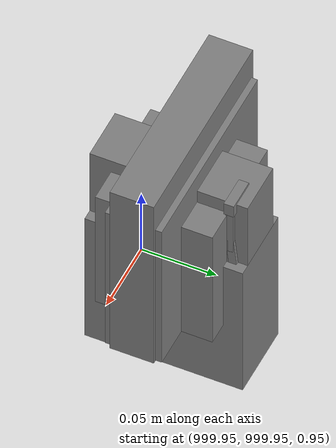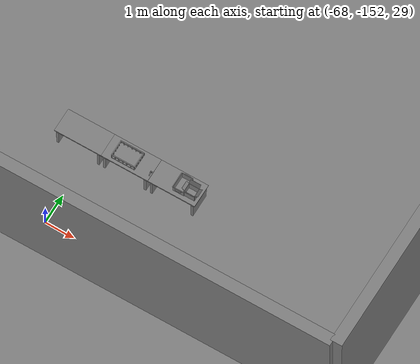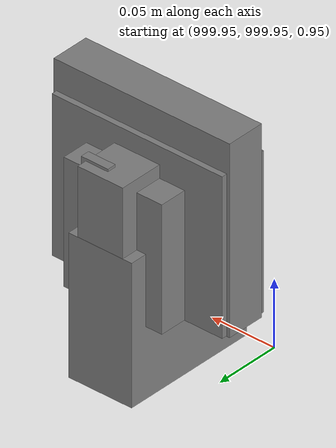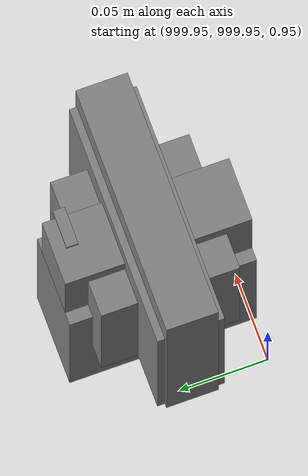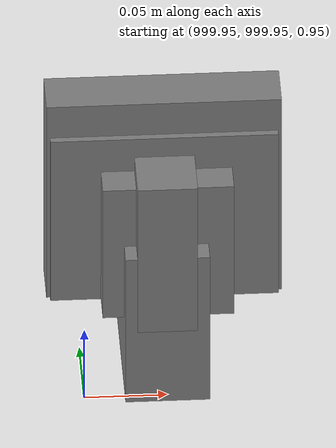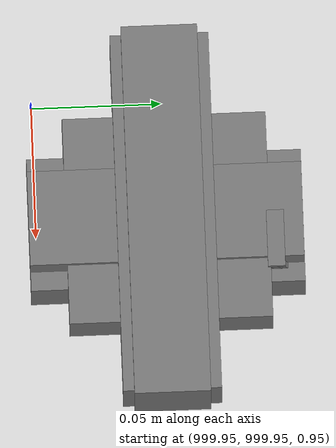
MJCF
<mujoco>
    <option gravity="0.000000000 0.000000000 -9.810000420" timestep="0.0049999999" integrator="implicitfast" density="1.225" viscosity="1.8000001e-05" noslip_iterations="10" iterations="100" sdf_iterations="50">
        <flag multiccd="disable"/>
    </option>
    <size memory="1000M"/>
    <compiler coordinate="local"/>
    <worldbody>
        <light cutoff="30" pos="0 1 1" dir="0 -1 -2"/>
        <light cutoff="30" pos="0 -1 1" dir="0 1 -2"/>
        <body pos="-64.866622925 -149.383972168 30.183746338" euler="89.999984741 89.999946594 0.000000000" name="openloong_gripper_2f85_fix_base_usda_bluebox_01">
            <geom contype="1" conaffinity="1" density="1000" type="box" material="" rgba="0.500000000 0.500000000 0.500000000 1.000000000" solimp="0.899999976 0.949999988 0.001000000" friction="1.000000000 0.005000000 0.000100000" solref="0.020000000 1.000000000" margin="0" condim="3" group="0" pos="0.276580811 0.187225342 0.000068665" quat="0.707106948 0.000077471 0.707106352 0.000077486" size="0.100000001 0.057999998 0.010000000" name="openloong_gripper_2f85_fix_base_usda_geom_3C45A59E_F66C_40C8_BC5E_88AC051D59B7"/>
            <geom contype="1" conaffinity="1" density="1000" type="box" material="" rgba="0.500000000 0.500000000 0.500000000 1.000000000" solimp="0.899999976 0.949999988 0.001000000" friction="1.000000000 0.005000000 0.000100000" solref="0.020000000 1.000000000" margin="0" condim="3" group="0" pos="0.000000000 0.002883911 0.000000000" quat="0.999999881 0.000000000 0.000000000 0.000000000" size="0.254000008 0.003000000 0.172000006" name="openloong_gripper_2f85_fix_base_usda_geom_C1D2CEB2_109D_4403_B5A0_8DE90400AC44"/>
            <geom contype="1" conaffinity="1" density="1000" type="box" material="" rgba="0.500000000 0.500000000 0.500000000 1.000000000" solimp="0.899999976 0.949999988 0.001000000" friction="1.000000000 0.005000000 0.000100000" solref="0.020000000 1.000000000" margin="0" condim="3" group="0" pos="0.000000000 0.124874115 0.173484802" quat="0.999796331 0.020176515 -0.000000015 0.000000030" size="0.259999990 0.119999997 0.007000000" name="openloong_gripper_2f85_fix_base_usda_geom_A8FC44D3_EBD1_4B86_8C68_15B7C14F0FDF"/>
            <geom contype="1" conaffinity="1" density="1000" type="box" material="" rgba="0.500000000 0.500000000 0.500000000 1.000000000" solimp="0.899999976 0.949999988 0.001000000" friction="1.000000000 0.005000000 0.000100000" solref="0.020000000 1.000000000" margin="0" condim="3" group="0" pos="0.000000000 0.124874115 -0.173469543" quat="0.999796331 -0.020176545 -0.000000015 0.000000000" size="0.259999990 0.119999997 0.007000000" name="openloong_gripper_2f85_fix_base_usda_geom_C834A073_67F2_4847_B138_C337F24DE534"/>
            <geom contype="1" conaffinity="1" density="1000" type="box" material="" rgba="0.500000000 0.500000000 0.500000000 1.000000000" solimp="0.899999976 0.949999988 0.001000000" friction="1.000000000 0.005000000 0.000100000" solref="0.020000000 1.000000000" margin="0" condim="3" group="0" pos="0.000000000 0.214008331 0.188980103" quat="0.999912977 0.013176724 0.000000015 0.000000000" size="0.259999990 0.029999999 0.012500000" name="openloong_gripper_2f85_fix_base_usda_geom_4DDCD1AE_7C6E_467B_8950_1CFC0592389B"/>
            <geom contype="1" conaffinity="1" density="1000" type="box" material="" rgba="0.500000000 0.500000000 0.500000000 1.000000000" solimp="0.899999976 0.949999988 0.001000000" friction="1.000000000 0.005000000 0.000100000" solref="0.020000000 1.000000000" margin="0" condim="3" group="0" pos="-0.258361816 0.125289917 0.001876831" quat="0.702796936 -0.020792112 0.710783124 0.020769298" size="0.189999998 0.119999997 0.009000000" name="openloong_gripper_2f85_fix_base_usda_geom_957A85CF_E9F7_47D1_956A_D3A754D8BD41"/>
            <geom contype="1" conaffinity="1" density="1000" type="box" material="" rgba="0.500000000 0.500000000 0.500000000 1.000000000" solimp="0.899999976 0.949999988 0.001000000" friction="1.000000000 0.005000000 0.000100000" solref="0.020000000 1.000000000" margin="0" condim="3" group="0" pos="0.000000000 0.214008331 -0.188980103" quat="0.999912977 -0.013176769 0.000000030 0.000000015" size="0.259999990 0.029999999 0.012500000" name="openloong_gripper_2f85_fix_base_usda_geom_D7DC6741_1DEA_4E27_894A_F77209380E24"/>
            <geom contype="1" conaffinity="1" density="1000" type="box" material="" rgba="0.500000000 0.500000000 0.500000000 1.000000000" solimp="0.899999976 0.949999988 0.001000000" friction="1.000000000 0.005000000 0.000100000" solref="0.020000000 1.000000000" margin="0" condim="3" group="0" pos="-0.276611328 0.187225342 0.000068665" quat="0.707106650 0.000077441 0.707106709 0.000077456" size="0.100000001 0.057999998 0.010000000" name="openloong_gripper_2f85_fix_base_usda_geom_8984BFAF_C231_4AB1_A6FF_739EC490B1C4"/>
            <geom contype="1" conaffinity="1" density="1000" type="box" material="" rgba="0.500000000 0.500000000 0.500000000 1.000000000" solimp="0.899999976 0.949999988 0.001000000" friction="1.000000000 0.005000000 0.000100000" solref="0.020000000 1.000000000" margin="0" condim="3" group="0" pos="0.258331299 0.125289917 0.001876831" quat="0.702851415 0.018856421 0.710823774 -0.019329369" size="0.189999998 0.119999997 0.009000000" name="openloong_gripper_2f85_fix_base_usda_geom_302B78AA_4A7D_498A_B0B6_2F5FC8B9ADB2"/>
            <freejoint name="openloong_gripper_2f85_fix_base_usda_bluebox_01_joint"/>
            <site size="0.005000000 0.005000000 0.005000000" rgba="0.500000000 0.500000000 0.500000000 1.000000000" pos="0.000000000 0.000000000 0.000000000" quat="0.999961913 0.008726534 0.000000000 0.000000000" group="0" type="sphere" name="openloong_gripper_2f85_fix_base_usda_bluebox_01site"/>
        </body>
        <body pos="-64.496299744 -149.491867065 30.235729218" euler="0.000000000 0.000000000 89.999946594" name="openloong_gripper_2f85_fix_base_usda_cardboardbox_01">
            <geom contype="1" conaffinity="1" density="1000" type="box" material="" rgba="0.500000000 0.500000000 0.500000000 1.000000000" solimp="0.899999976 0.949999988 0.001000000" friction="1.000000000 0.005000000 0.000100000" solref="0.020000000 1.000000000" margin="0" condim="3" group="0" pos="-0.003166199 -0.004086494 0.005052090" quat="1.000000000 0.000000000 0.000000000 0.000000000" size="0.142499998 0.177500010 0.005000000" name="openloong_gripper_2f85_fix_base_usda_geom_D9974F4C_053F_423D_8F46_DE2A4AE91F9E"/>
            <geom contype="1" conaffinity="1" density="1000" type="box" material="" rgba="0.500000000 0.500000000 0.500000000 1.000000000" solimp="0.899999976 0.949999988 0.001000000" friction="1.000000000 0.005000000 0.000100000" solref="0.020000000 1.000000000" margin="0" condim="3" group="0" pos="-0.003166199 0.170316696 0.150570869" quat="1.000000000 0.000000000 0.000000000 0.000000000" size="0.142499998 0.005000000 0.149999991" name="openloong_gripper_2f85_fix_base_usda_geom_A1082EC3_08A6_468B_81B2_84168E3B1B61"/>
            <geom contype="1" conaffinity="1" density="1000" type="box" material="" rgba="0.500000000 0.500000000 0.500000000 1.000000000" solimp="0.899999976 0.949999988 0.001000000" friction="1.000000000 0.005000000 0.000100000" solref="0.020000000 1.000000000" margin="0" condim="3" group="0" pos="-0.147399902 -0.005307198 0.150570869" quat="1.000000000 0.000000000 0.000000000 0.000000000" size="0.005000000 0.177500010 0.149999991" name="openloong_gripper_2f85_fix_base_usda_geom_E02DBB4F_8174_4726_8A0D_0E066EB802A4"/>
            <geom contype="1" conaffinity="1" density="1000" type="box" material="" rgba="0.500000000 0.500000000 0.500000000 1.000000000" solimp="0.899999976 0.949999988 0.001000000" friction="1.000000000 0.005000000 0.000100000" solref="0.020000000 1.000000000" margin="0" condim="3" group="0" pos="0.140275955 -0.005307198 0.150570869" quat="1.000000000 0.000000000 0.000000000 0.000000000" size="0.005000000 0.177500010 0.149999991" name="openloong_gripper_2f85_fix_base_usda_geom_0B490FA5_589B_431B_AEEC_60914410B8AA"/>
            <geom contype="1" conaffinity="1" density="1000" type="box" material="" rgba="0.500000000 0.500000000 0.500000000 1.000000000" solimp="0.899999976 0.949999988 0.001000000" friction="1.000000000 0.005000000 0.000100000" solref="0.020000000 1.000000000" margin="0" condim="3" group="0" pos="-0.003166199 -0.181550980 0.150570869" quat="1.000000000 0.000000000 0.000000000 0.000000000" size="0.142499998 0.005000000 0.149999991" name="openloong_gripper_2f85_fix_base_usda_geom_B5179D32_0465_4587_A3F5_DC1EC2706EB5"/>
            <freejoint name="openloong_gripper_2f85_fix_base_usda_cardboardbox_01_joint"/>
            <site size="0.005000000 0.005000000 0.005000000" rgba="0.500000000 0.500000000 0.500000000 1.000000000" pos="0.000000000 0.000000000 0.000000000" quat="0.999961913 0.008726535 0.000000000 0.000000000" group="0" type="sphere" name="openloong_gripper_2f85_fix_base_usda_site_2CB30CBD_CCB3_4B73_A69D_89619429F84A"/>
            <body pos="0.139160156 -0.004048347 0.301930904" euler="-179.999954224 49.383502960 179.999954224" name="openloong_gripper_2f85_fix_base_usda_A1_006">
                <geom contype="1" conaffinity="1" density="1000" type="box" material="" rgba="0.500000000 0.500000000 0.500000000 1.000000000" solimp="0.899999976 0.949999988 0.001000000" friction="1.000000000 0.005000000 0.000100000" solref="0.020000000 1.000000000" margin="0" condim="3" group="0" pos="-0.071587563 0.000009537 0.001745224" quat="0.999999881 0.000000000 0.000000000 0.000000000" size="0.071249999 0.179999992 0.002500000" name="openloong_gripper_2f85_fix_base_usda_geom_E9988E68_8487_4337_84D7_C161BEBF7012"/>
                <joint armature="0" stiffness="0.07" damping="0.0099999998" axis="0.000000 1.000000 0.000000" type="hinge" name="openloong_gripper_2f85_fix_base_usda_A1_006"/>
            </body>
            <body pos="-0.145902634 -0.004086494 0.301938057" euler="-180.000000000 -60.000011444 -180.000000000" name="openloong_gripper_2f85_fix_base_usda_A2_006">
                <geom contype="1" conaffinity="1" density="1000" type="box" material="" rgba="0.500000000 0.500000000 0.500000000 1.000000000" solimp="0.899999976 0.949999988 0.001000000" friction="1.000000000 0.005000000 0.000100000" solref="0.020000000 1.000000000" margin="0" condim="3" group="0" pos="0.071268082 0.000009537 0.002717972" quat="0.000002921 0.000000000 -0.000000030 0.999999881" size="0.071249999 0.179999992 0.002500000" name="openloong_gripper_2f85_fix_base_usda_geom_EBB2B40E_4B40_4FDC_AAC2_671E747D4F7A"/>
                <joint armature="0" stiffness="0.07" damping="0.0099999998" axis="0.000000 1.000000 0.000000" type="hinge" name="openloong_gripper_2f85_fix_base_usda_A2_006"/>
            </body>
            <body pos="-0.003385544 0.175991058 0.301930904" euler="-125.858116150 -0.000004561 0.000002331" name="openloong_gripper_2f85_fix_base_usda_B2_006">
                <geom contype="1" conaffinity="1" density="1000" type="box" material="" rgba="0.500000000 0.500000000 0.500000000 1.000000000" solimp="0.899999976 0.949999988 0.001000000" friction="1.000000000 0.005000000 0.000100000" solref="0.020000000 1.000000000" margin="0" condim="3" group="0" pos="0.000009537 -0.070939064 -0.002470016" quat="0.999614120 0.027776197 -0.000000015 0.000000030" size="0.137500003 0.064999998 0.005000000" name="openloong_gripper_2f85_fix_base_usda_geom_A8E8DBA1_8CB9_402C_BBBB_777E25107070"/>
                <joint armature="0" stiffness="0.07" damping="0.0099999998" axis="1.000000 0.000000 0.000000" type="hinge" name="openloong_gripper_2f85_fix_base_usda_B2_006"/>
            </body>
            <body pos="-0.003385544 -0.184140205 0.301938057" euler="147.805557251 0.000000000 0.000000000" name="openloong_gripper_2f85_fix_base_usda_B1_006">
                <geom contype="1" conaffinity="1" density="1000" type="box" material="" rgba="0.500000000 0.500000000 0.500000000 1.000000000" solimp="0.899999976 0.949999988 0.001000000" friction="1.000000000 0.005000000 0.000100000" solref="0.020000000 1.000000000" margin="0" condim="3" group="0" pos="-0.000028610 0.070202351 -0.002703667" quat="0.999614179 -0.027776167 0.000000000 0.000000000" size="0.137500003 0.064999998 0.005000000" name="openloong_gripper_2f85_fix_base_usda_geom_D4BE1960_6E25_4065_89EF_5F4949B19FB1"/>
                <joint armature="0" stiffness="0.07" damping="0.0099999998" axis="1.000000 0.000000 0.000000" type="hinge" name="openloong_gripper_2f85_fix_base_usda_B1_006"/>
            </body>
        </body>
        <body pos="-65.882858276 -149.481979370 30.229999542" euler="-64.487716675 0.000000000 0.000000000" name="openloong_gripper_2f85_fix_base_usda_Barcode">
            <geom contype="1" conaffinity="1" density="1000" type="box" material="" rgba="0.500000000 0.500000000 0.500000000 1.000000000" solimp="0.899999976 0.949999988 0.001000000" friction="1.000000000 0.005000000 0.000100000" solref="0.020000000 1.000000000" margin="0" condim="3" group="0" pos="0.000000000 0.013038635 0.001419067" quat="0.000000000 0.000000000 0.000000000 1.000000119" size="0.034000002 0.010000000 0.017999999" name="openloong_gripper_2f85_fix_base_usda_geom_B5801274_2F05_48C6_BADC_64F5FA58B8B0"/>
            <geom contype="1" conaffinity="1" density="1000" type="box" material="" rgba="0.500000000 0.500000000 0.500000000 1.000000000" solimp="0.899999976 0.949999988 0.001000000" friction="1.000000000 0.005000000 0.000100000" solref="0.020000000 1.000000000" margin="0" condim="3" group="0" pos="0.000000000 -0.035301208 -0.007095337" quat="0.000000000 0.000000000 -0.043619365 0.999048233" size="0.028999999 0.010000000 0.020000000" name="openloong_gripper_2f85_fix_base_usda_geom_F9FA3349_5F2F_475F_BA20_23CF2D1DB899"/>
            <geom contype="1" conaffinity="1" density="1000" type="box" material="" rgba="0.500000000 0.500000000 0.500000000 1.000000000" solimp="0.899999976 0.949999988 0.001000000" friction="1.000000000 0.005000000 0.000100000" solref="0.020000000 1.000000000" margin="0" condim="3" group="0" pos="0.000000000 -0.043411255 -0.011749268" quat="0.922262907 0.386563420 0.000000000 0.000000000" size="0.026000001 0.010000000 0.020000000" name="openloong_gripper_2f85_fix_base_usda_geom_A3EA1E78_AF66_479D_9167_3A57AAF681AE"/>
            <geom contype="1" conaffinity="1" density="1000" type="box" material="" rgba="0.500000000 0.500000000 0.500000000 1.000000000" solimp="0.899999976 0.949999988 0.001000000" friction="1.000000000 0.005000000 0.000100000" solref="0.020000000 1.000000000" margin="0" condim="3" group="0" pos="0.000000000 -0.016967773 -0.031860352" quat="0.000000000 0.000000000 0.000000000 1.000000119" size="0.008000000 0.010000000 0.013000000" name="openloong_gripper_2f85_fix_base_usda_geom_6B4640C5_BCCE_4B18_9D66_CAFCB1D13A2E"/>
            <geom contype="1" conaffinity="1" density="1000" type="box" material="" rgba="0.500000000 0.500000000 0.500000000 1.000000000" solimp="0.899999976 0.949999988 0.001000000" friction="1.000000000 0.005000000 0.000100000" solref="0.020000000 1.000000000" margin="0" condim="3" group="0" pos="0.000000000 -0.001869202 0.000312805" quat="0.953716993 0.300705761 0.000000000 0.000000000" size="0.032000002 0.010000000 0.018999999" name="openloong_gripper_2f85_fix_base_usda_geom_4E9DADFF_9E82_4DA7_9274_5BAA60332C31"/>
            <geom contype="1" conaffinity="1" density="1000" type="box" material="" rgba="0.500000000 0.500000000 0.500000000 1.000000000" solimp="0.899999976 0.949999988 0.001000000" friction="1.000000000 0.005000000 0.000100000" solref="0.020000000 1.000000000" margin="0" condim="3" group="0" pos="0.000000000 -0.019531250 -0.003173828" quat="0.953716993 0.300705761 0.000000000 0.000000000" size="0.030999999 0.010000000 0.020000000" name="openloong_gripper_2f85_fix_base_usda_geom_E946E090_A3BE_45C2_B837_56422C511669"/>
            <geom contype="1" conaffinity="1" density="1000" type="box" material="" rgba="0.500000000 0.500000000 0.500000000 1.000000000" solimp="0.899999976 0.949999988 0.001000000" friction="1.000000000 0.005000000 0.000100000" solref="0.020000000 1.000000000" margin="0" condim="3" group="0" pos="0.000000000 -0.035301208 -0.007095337" quat="0.953716993 0.300705761 0.000000000 0.000000000" size="0.028999999 0.010000000 0.020000000" name="openloong_gripper_2f85_fix_base_usda_geom_B38E31DE_AB76_4411_B8A5_0DAEB857E5D3"/>
            <geom contype="1" conaffinity="1" density="1000" type="box" material="" rgba="0.500000000 0.500000000 0.500000000 1.000000000" solimp="0.899999976 0.949999988 0.001000000" friction="1.000000000 0.005000000 0.000100000" solref="0.020000000 1.000000000" margin="0" condim="3" group="0" pos="0.000000000 -0.042617798 -0.071121216" quat="0.000000000 0.000000000 0.000000000 1.000000119" size="0.013000000 0.021000000 0.059999999" name="openloong_gripper_2f85_fix_base_usda_geom_384E3623_681E_452D_8D1D_E9D97DDA0FAF"/>
            <freejoint name="openloong_gripper_2f85_fix_base_usda_Barcode_joint"/>
            <site size="0.005000000 0.005000000 0.005000000" rgba="0.500000000 0.500000000 0.500000000 1.000000000" pos="0.000000000 0.000000000 0.000000000" quat="1.000000000 0.000000000 0.000000000 0.000000000" group="0" type="sphere" name="openloong_gripper_2f85_fix_base_usda_Barcode_site"/>
        </body>
        <body pos="-66.745018005 -149.392349243 30.184000015" euler="0.000000000 0.000000000 89.999946594" name="[22330280667257]_Basket_01">
            <geom contype="1" conaffinity="1" density="1000" type="box" material="" rgba="0.500000000 0.500000000 0.500000000 1.000000000" solimp="0.899999976 0.949999988 0.001000000" friction="1.000000000 0.005000000 0.000100000" solref="0.020000000 1.000000000" margin="0" condim="3" group="0" pos="-0.052425385 0.389207840 0.089787483" quat="0.707107008 0.000000000 0.000000000 0.707106411" size="0.014249999 0.014249999 0.059999999" name="[22330280667257]_geom_B4E73FF5_2C9B_47B6_9D92_B62DFD811287"/>
            <geom contype="1" conaffinity="1" density="1000" type="box" material="" rgba="0.500000000 0.500000000 0.500000000 1.000000000" solimp="0.899999976 0.949999988 0.001000000" friction="1.000000000 0.005000000 0.000100000" solref="0.020000000 1.000000000" margin="0" condim="3" group="0" pos="0.264015198 -0.133043289 0.089787483" quat="0.707107008 0.000000000 0.000000000 0.707106411" size="0.014249999 0.014249999 0.059999999" name="[22330280667257]_geom_D56D01E2_E391_4CB2_8D5E_AFB278430508"/>
            <geom contype="1" conaffinity="1" density="1000" type="box" material="" rgba="0.500000000 0.500000000 0.500000000 1.000000000" solimp="0.899999976 0.949999988 0.001000000" friction="1.000000000 0.005000000 0.000100000" solref="0.020000000 1.000000000" margin="0" condim="3" group="0" pos="-0.264015198 -0.265548706 0.089793205" quat="0.707107008 0.000000000 0.000000000 0.707106411" size="0.014249999 0.014249999 0.059999999" name="[22330280667257]_geom_1E41288A_0E66_413A_B7F0_E1341DCABDC7"/>
            <geom contype="1" conaffinity="1" density="1000" type="box" material="" rgba="0.500000000 0.500000000 0.500000000 1.000000000" solimp="0.899999976 0.949999988 0.001000000" friction="1.000000000 0.005000000 0.000100000" solref="0.020000000 1.000000000" margin="0" condim="3" group="0" pos="-0.160263062 -0.389322281 0.089793205" quat="0.707107008 0.000000000 0.000000000 0.707106411" size="0.014249999 0.014249999 0.059999999" name="[22330280667257]_geom_240A234E_6834_483C_8E0D_3B5E50CAEE4B"/>
            <geom contype="1" conaffinity="1" density="1000" type="box" material="" rgba="0.500000000 0.500000000 0.500000000 1.000000000" solimp="0.899999976 0.949999988 0.001000000" friction="1.000000000 0.005000000 0.000100000" solref="0.020000000 1.000000000" margin="0" condim="3" group="0" pos="0.162265778 -0.389322281 0.089787483" quat="0.707107008 0.000000000 0.000000000 0.707106411" size="0.014249999 0.014249999 0.059999999" name="[22330280667257]_geom_DA3A14D1_374A_483E_A954_E2A823728C94"/>
            <geom contype="1" conaffinity="1" density="1000" type="box" material="" rgba="0.500000000 0.500000000 0.500000000 1.000000000" solimp="0.899999976 0.949999988 0.001000000" friction="1.000000000 0.005000000 0.000100000" solref="0.020000000 1.000000000" margin="0" condim="3" group="0" pos="0.264015198 0.389207840 0.089787483" quat="0.707107008 0.000000000 0.000000000 0.707106411" size="0.014249999 0.014249999 0.059999999" name="[22330280667257]_geom_43CED7D8_0935_4EAD_B62F_D2973B121E08"/>
            <geom contype="1" conaffinity="1" density="1000" type="box" material="" rgba="0.500000000 0.500000000 0.500000000 1.000000000" solimp="0.899999976 0.949999988 0.001000000" friction="1.000000000 0.005000000 0.000100000" solref="0.020000000 1.000000000" margin="0" condim="3" group="0" pos="-0.264015198 -0.133043289 0.089793205" quat="0.707107008 0.000000000 0.000000000 0.707106411" size="0.014249999 0.014249999 0.059999999" name="[22330280667257]_geom_373F42BB_712C_464E_A73E_6B6ADD8E2FFF"/>
            <geom contype="1" conaffinity="1" density="1000" type="box" material="" rgba="0.500000000 0.500000000 0.500000000 1.000000000" solimp="0.899999976 0.949999988 0.001000000" friction="1.000000000 0.005000000 0.000100000" solref="0.020000000 1.000000000" margin="0" condim="3" group="0" pos="-0.264026642 0.269256592 0.089793205" quat="0.707107008 0.000000000 0.000000000 0.707106411" size="0.014249999 0.014249999 0.059999999" name="[22330280667257]_geom_A27DA147_7030_49C1_B113_6CF4CD89DEA2"/>
            <geom contype="1" conaffinity="1" density="1000" type="box" material="" rgba="0.500000000 0.500000000 0.500000000 1.000000000" solimp="0.899999976 0.949999988 0.001000000" friction="1.000000000 0.005000000 0.000100000" solref="0.020000000 1.000000000" margin="0" condim="3" group="0" pos="0.054462433 0.389207840 0.089787483" quat="0.707107008 0.000000000 0.000000000 0.707106411" size="0.014249999 0.014249999 0.059999999" name="[22330280667257]_geom_98C0B60B_1F13_4572_B4DB_0D313C882457"/>
            <geom contype="1" conaffinity="1" density="1000" type="box" material="" rgba="0.500000000 0.500000000 0.500000000 1.000000000" solimp="0.899999976 0.949999988 0.001000000" friction="1.000000000 0.005000000 0.000100000" solref="0.020000000 1.000000000" margin="0" condim="3" group="0" pos="0.054462433 -0.389322281 0.089787483" quat="0.707107008 0.000000000 0.000000000 0.707106411" size="0.014249999 0.014249999 0.059999999" name="[22330280667257]_geom_72520B5E_C5EE_410A_B6B6_CC0C9B5E2F7F"/>
            <geom contype="1" conaffinity="1" density="1000" type="box" material="" rgba="0.500000000 0.500000000 0.500000000 1.000000000" solimp="0.899999976 0.949999988 0.001000000" friction="1.000000000 0.005000000 0.000100000" solref="0.020000000 1.000000000" margin="0" condim="3" group="0" pos="0.264015198 0.269256592 0.089793205" quat="0.707107008 0.000000000 0.000000000 0.707106411" size="0.014249999 0.014249999 0.059999999" name="[22330280667257]_geom_9155DA2F_C949_440E_834A_39CCBB02DBC1"/>
            <geom contype="1" conaffinity="1" density="1000" type="box" material="" rgba="0.500000000 0.500000000 0.500000000 1.000000000" solimp="0.899999976 0.949999988 0.001000000" friction="1.000000000 0.005000000 0.000100000" solref="0.020000000 1.000000000" margin="0" condim="3" group="0" pos="0.264015198 -0.389322281 0.089787483" quat="0.707107008 0.000000000 0.000000000 0.707106411" size="0.014249999 0.014249999 0.059999999" name="[22330280667257]_geom_F9D2B94F_663C_46C5_8C79_D9D2D2B716C6"/>
            <geom contype="1" conaffinity="1" density="1000" type="box" material="" rgba="0.500000000 0.500000000 0.500000000 1.000000000" solimp="0.899999976 0.949999988 0.001000000" friction="1.000000000 0.005000000 0.000100000" solref="0.020000000 1.000000000" margin="0" condim="3" group="0" pos="0.000000000 0.000000000 0.015998840" quat="0.707107008 0.000000000 0.000000000 0.707106411" size="0.403499991 0.279000014 0.015750000" name="[22330280667257]_geom_30701EB7_4490_4B61_AB2F_7978ABA8B3D5"/>
            <geom contype="1" conaffinity="1" density="1000" type="box" material="" rgba="0.500000000 0.500000000 0.500000000 1.000000000" solimp="0.899999976 0.949999988 0.001000000" friction="1.000000000 0.005000000 0.000100000" solref="0.020000000 1.000000000" margin="0" condim="3" group="0" pos="0.000000000 -0.389476776 0.163619041" quat="0.707107008 0.000000000 0.000000000 0.707106411" size="0.015000000 0.277500004 0.015750000" name="[22330280667257]_geom_1E6C2023_1042_4EF4_A022_587146CBC7EA"/>
            <geom contype="1" conaffinity="1" density="1000" type="box" material="" rgba="0.500000000 0.500000000 0.500000000 1.000000000" solimp="0.899999976 0.949999988 0.001000000" friction="1.000000000 0.005000000 0.000100000" solref="0.020000000 1.000000000" margin="0" condim="3" group="0" pos="0.162265778 0.389207840 0.089787483" quat="0.707107008 0.000000000 0.000000000 0.707106411" size="0.014249999 0.014249999 0.059999999" name="[22330280667257]_geom_AAB5C420_54B0_4906_8BA2_5F71AEB9917A"/>
            <geom contype="1" conaffinity="1" density="1000" type="box" material="" rgba="0.500000000 0.500000000 0.500000000 1.000000000" solimp="0.899999976 0.949999988 0.001000000" friction="1.000000000 0.005000000 0.000100000" solref="0.020000000 1.000000000" margin="0" condim="3" group="0" pos="0.000000000 0.389471054 0.163619041" quat="0.707107008 0.000000000 0.000000000 0.707106411" size="0.015000000 0.277500004 0.015750000" name="[22330280667257]_geom_58527F4F_553E_4D72_A3F0_EF6DC912B136"/>
            <geom contype="1" conaffinity="1" density="1000" type="box" material="" rgba="0.500000000 0.500000000 0.500000000 1.000000000" solimp="0.899999976 0.949999988 0.001000000" friction="1.000000000 0.005000000 0.000100000" solref="0.020000000 1.000000000" margin="0" condim="3" group="0" pos="-0.263511658 0.000000000 0.163619041" quat="0.707107008 0.000000000 0.000000000 0.707106411" size="0.403499991 0.015000000 0.015750000" name="[22330280667257]_geom_4D864EE2_BE2F_4600_9202_8EC9A4EEF667"/>
            <geom contype="1" conaffinity="1" density="1000" type="box" material="" rgba="0.500000000 0.500000000 0.500000000 1.000000000" solimp="0.899999976 0.949999988 0.001000000" friction="1.000000000 0.005000000 0.000100000" solref="0.020000000 1.000000000" margin="0" condim="3" group="0" pos="-0.264015198 0.141334534 0.089793205" quat="0.707107008 0.000000000 0.000000000 0.707106411" size="0.014249999 0.014249999 0.059999999" name="[22330280667257]_geom_58BB49A5_0C13_4FC6_AD95_2F5596B81976"/>
            <geom contype="1" conaffinity="1" density="1000" type="box" material="" rgba="0.500000000 0.500000000 0.500000000 1.000000000" solimp="0.899999976 0.949999988 0.001000000" friction="1.000000000 0.005000000 0.000100000" solref="0.020000000 1.000000000" margin="0" condim="3" group="0" pos="0.264015198 -0.265548706 0.089787483" quat="0.707107008 0.000000000 0.000000000 0.707106411" size="0.014249999 0.014249999 0.059999999" name="[22330280667257]_geom_D93DA073_20DC_4915_B98D_2BA66201D665"/>
            <geom contype="1" conaffinity="1" density="1000" type="box" material="" rgba="0.500000000 0.500000000 0.500000000 1.000000000" solimp="0.899999976 0.949999988 0.001000000" friction="1.000000000 0.005000000 0.000100000" solref="0.020000000 1.000000000" margin="0" condim="3" group="0" pos="-0.160263062 0.389207840 0.089787483" quat="0.707107008 0.000000000 0.000000000 0.707106411" size="0.014249999 0.014249999 0.059999999" name="[22330280667257]_geom_3559BEBA_1275_4B4F_9212_DAF85F498527"/>
            <geom contype="1" conaffinity="1" density="1000" type="box" material="" rgba="0.500000000 0.500000000 0.500000000 1.000000000" solimp="0.899999976 0.949999988 0.001000000" friction="1.000000000 0.005000000 0.000100000" solref="0.020000000 1.000000000" margin="0" condim="3" group="0" pos="-0.052425385 -0.389322281 0.089787483" quat="0.707107008 0.000000000 0.000000000 0.707106411" size="0.014249999 0.014249999 0.059999999" name="[22330280667257]_geom_9BF02B8E_B727_45CB_A0A7_8F80037121AF"/>
            <geom contype="1" conaffinity="1" density="1000" type="box" material="" rgba="0.500000000 0.500000000 0.500000000 1.000000000" solimp="0.899999976 0.949999988 0.001000000" friction="1.000000000 0.005000000 0.000100000" solref="0.020000000 1.000000000" margin="0" condim="3" group="0" pos="-0.264026642 -0.389322281 0.089793205" quat="0.707107008 0.000000000 0.000000000 0.707106411" size="0.014249999 0.014249999 0.059999999" name="[22330280667257]_geom_6A28518D_9BA7_4211_8BE1_984E553293D5"/>
            <geom contype="1" conaffinity="1" density="1000" type="box" material="" rgba="0.500000000 0.500000000 0.500000000 1.000000000" solimp="0.899999976 0.949999988 0.001000000" friction="1.000000000 0.005000000 0.000100000" solref="0.020000000 1.000000000" margin="0" condim="3" group="0" pos="0.264015198 0.141334534 0.089787483" quat="0.707107008 0.000000000 0.000000000 0.707106411" size="0.014249999 0.014249999 0.059999999" name="[22330280667257]_geom_FDD23A16_96F8_4089_9C0F_DFD43CEC41EB"/>
            <geom contype="1" conaffinity="1" density="1000" type="box" material="" rgba="0.500000000 0.500000000 0.500000000 1.000000000" solimp="0.899999976 0.949999988 0.001000000" friction="1.000000000 0.005000000 0.000100000" solref="0.020000000 1.000000000" margin="0" condim="3" group="0" pos="-0.264015198 0.389207840 0.089793205" quat="0.707107008 0.000000000 0.000000000 0.707106411" size="0.014249999 0.014249999 0.059999999" name="[22330280667257]_geom_416CBF85_D02B_460B_B830_863DEAF9B2BF"/>
            <geom contype="1" conaffinity="1" density="1000" type="box" material="" rgba="0.500000000 0.500000000 0.500000000 1.000000000" solimp="0.899999976 0.949999988 0.001000000" friction="1.000000000 0.005000000 0.000100000" solref="0.020000000 1.000000000" margin="0" condim="3" group="0" pos="0.264015198 0.004480362 0.089787483" quat="0.707107008 0.000000000 0.000000000 0.707106411" size="0.014249999 0.014249999 0.059999999" name="[22330280667257]_geom_233A7708_486A_4306_BA2A_7E5B366E3A05"/>
            <geom contype="1" conaffinity="1" density="1000" type="box" material="" rgba="0.500000000 0.500000000 0.500000000 1.000000000" solimp="0.899999976 0.949999988 0.001000000" friction="1.000000000 0.005000000 0.000100000" solref="0.020000000 1.000000000" margin="0" condim="3" group="0" pos="0.263694763 -0.000011444 0.163619041" quat="0.707107008 0.000000000 0.000000000 0.707106411" size="0.403499991 0.015000000 0.015750000" name="[22330280667257]_geom_4E34EF6E_A9C5_44B9_BE81_40FB86069BF0"/>
            <geom contype="1" conaffinity="1" density="1000" type="box" material="" rgba="0.500000000 0.500000000 0.500000000 1.000000000" solimp="0.899999976 0.949999988 0.001000000" friction="1.000000000 0.005000000 0.000100000" solref="0.020000000 1.000000000" margin="0" condim="3" group="0" pos="-0.264015198 0.004480362 0.089793205" quat="0.707107008 0.000000000 0.000000000 0.707106411" size="0.014249999 0.014249999 0.059999999" name="[22330280667257]_geom_6C095600_6AC8_4806_ABAE_404DA2A03562"/>
            <freejoint name="[22330280667257]_joint_6850F0A1_C139_4BE2_AB5E_55E429774237"/>
        </body>
        <body pos="0.000000000 0.000000000 0.000000000" euler="0.000000000 0.000000000 0.000000000" name="Static Objects_Static Objects">
            <geom contype="1" conaffinity="1" density="1000" type="box" material="" rgba="0.500000000 0.500000000 0.500000000 1.000000000" solimp="0.899999976 0.949999988 0.001000000" friction="1.000000000 0.005000000 0.000100000" solref="0.020000000 1.000000000" margin="0" condim="3" group="0" pos="-67.544113159 -149.365814209 29.727830887" quat="0.500000417 0.499999970 0.499999553 0.499999970" size="0.381000012 0.319999993 0.041000001" name="Static Objects_geom_91B74634_FB1A_438D_8BC5_D8D0180C496F"/>
            <geom contype="1" conaffinity="1" density="1000" type="box" material="" rgba="0.500000000 0.500000000 0.500000000 1.000000000" solimp="0.899999976 0.949999988 0.001000000" friction="1.000000000 0.005000000 0.000100000" solref="0.020000000 1.000000000" margin="0" condim="3" group="0" pos="-68.239501953 -149.365814209 30.086868286" quat="0.500000417 0.499999970 0.499999553 0.499999970" size="0.370999992 0.039500002 0.745000005" name="Static Objects_geom_EF8AE837_B8BD_454C_9550_F461019B2127"/>
            <geom contype="1" conaffinity="1" density="1000" type="box" material="" rgba="0.500000000 0.500000000 0.500000000 1.000000000" solimp="0.899999976 0.949999988 0.001000000" friction="1.000000000 0.005000000 0.000100000" solref="0.020000000 1.000000000" margin="0" condim="3" group="0" pos="-68.239501953 -149.365814209 30.147235870" quat="0.500000417 0.499999970 0.499999553 0.499999970" size="0.400000006 0.022000000 0.800000012" name="Static Objects_geom_D888C095_D9DB_4683_A95E_363A07979A50"/>
            <geom contype="1" conaffinity="1" density="1000" type="box" material="" rgba="0.500000000 0.500000000 0.500000000 1.000000000" solimp="0.899999976 0.949999988 0.001000000" friction="1.000000000 0.005000000 0.000100000" solref="0.020000000 1.000000000" margin="0" condim="3" group="0" pos="-68.934890747 -149.365814209 29.727830887" quat="0.500000417 0.499999970 0.499999553 0.499999970" size="0.381000012 0.319999993 0.041000001" name="Static Objects_geom_A92FEA53_814F_4CF8_9BF6_B95ED5951961"/>
            <geom contype="1" conaffinity="1" density="1000" type="box" material="" rgba="0.500000000 0.500000000 0.500000000 1.000000000" solimp="0.899999976 0.949999988 0.001000000" friction="1.000000000 0.005000000 0.000100000" solref="0.020000000 1.000000000" margin="0" condim="3" group="0" pos="-68.239501953 -149.365814209 29.561563492" quat="0.500000417 0.499999970 0.499999553 0.499999970" size="0.020000000 0.022000000 0.660000026" name="Static Objects_geom_C0A4057B_F991_44E1_81BF_A8C58EC7F99C"/>
            <geom contype="1" conaffinity="1" density="1000" type="box" material="" rgba="0.500000000 0.500000000 0.500000000 1.000000000" solimp="0.899999976 0.949999988 0.001000000" friction="1.000000000 0.005000000 0.000100000" solref="0.020000000 1.000000000" margin="0" condim="3" group="0" pos="-65.945671082 -149.365814209 29.727830887" quat="0.500000417 0.499999970 0.499999553 0.499999970" size="0.381000012 0.319999993 0.041000001" name="Static Objects_geom_0E3EEACA_E4EC_49A0_BB8A_CEFBA2840230"/>
            <geom contype="1" conaffinity="1" density="1000" type="box" material="" rgba="0.500000000 0.500000000 0.500000000 1.000000000" solimp="0.899999976 0.949999988 0.001000000" friction="1.000000000 0.005000000 0.000100000" solref="0.020000000 1.000000000" margin="0" condim="3" group="0" pos="-66.641059875 -149.365814209 30.086868286" quat="0.500000417 0.499999970 0.499999553 0.499999970" size="0.370999992 0.039500002 0.745000005" name="Static Objects_geom_3D5F680C_F4C5_4A44_96D7_ACAC2BBCE4AA"/>
            <geom contype="1" conaffinity="1" density="1000" type="box" material="" rgba="0.500000000 0.500000000 0.500000000 1.000000000" solimp="0.899999976 0.949999988 0.001000000" friction="1.000000000 0.005000000 0.000100000" solref="0.020000000 1.000000000" margin="0" condim="3" group="0" pos="-66.641059875 -149.365814209 30.147235870" quat="0.500000417 0.499999970 0.499999553 0.499999970" size="0.400000006 0.022000000 0.800000012" name="Static Objects_geom_353959A0_504B_48A3_B1B5_E2B89BF7A688"/>
            <geom contype="1" conaffinity="1" density="1000" type="box" material="" rgba="0.500000000 0.500000000 0.500000000 1.000000000" solimp="0.899999976 0.949999988 0.001000000" friction="1.000000000 0.005000000 0.000100000" solref="0.020000000 1.000000000" margin="0" condim="3" group="0" pos="-67.336448669 -149.365814209 29.727830887" quat="0.500000417 0.499999970 0.499999553 0.499999970" size="0.381000012 0.319999993 0.041000001" name="Static Objects_geom_1C17AB58_DA4F_415C_B06D_93B8C3B04D45"/>
            <geom contype="1" conaffinity="1" density="1000" type="box" material="" rgba="0.500000000 0.500000000 0.500000000 1.000000000" solimp="0.899999976 0.949999988 0.001000000" friction="1.000000000 0.005000000 0.000100000" solref="0.020000000 1.000000000" margin="0" condim="3" group="0" pos="-66.641059875 -149.365814209 29.561563492" quat="0.500000417 0.499999970 0.499999553 0.499999970" size="0.020000000 0.022000000 0.660000026" name="Static Objects_geom_55310FC4_6DA6_419B_8AA9_EDECCDC0FE5C"/>
            <geom contype="1" conaffinity="1" density="1000" type="box" material="" rgba="0.500000000 0.500000000 0.500000000 1.000000000" solimp="0.899999976 0.949999988 0.001000000" friction="1.000000000 0.005000000 0.000100000" solref="0.020000000 1.000000000" margin="0" condim="3" group="0" pos="-64.338577271 -149.365814209 29.727830887" quat="0.500000417 0.499999970 0.499999553 0.499999970" size="0.381000012 0.319999993 0.041000001" name="Static Objects_geom_416394B7_CC7C_4676_B5B2_9439BB255847"/>
            <geom contype="1" conaffinity="1" density="1000" type="box" material="" rgba="0.500000000 0.500000000 0.500000000 1.000000000" solimp="0.899999976 0.949999988 0.001000000" friction="1.000000000 0.005000000 0.000100000" solref="0.020000000 1.000000000" margin="0" condim="3" group="0" pos="-65.033966064 -149.365814209 30.086868286" quat="0.500000417 0.499999970 0.499999553 0.499999970" size="0.370999992 0.039500002 0.745000005" name="Static Objects_geom_19C294CE_93D7_42D0_A8EC_AC414A583679"/>
            <geom contype="1" conaffinity="1" density="1000" type="box" material="" rgba="0.500000000 0.500000000 0.500000000 1.000000000" solimp="0.899999976 0.949999988 0.001000000" friction="1.000000000 0.005000000 0.000100000" solref="0.020000000 1.000000000" margin="0" condim="3" group="0" pos="-65.033966064 -149.365814209 30.147235870" quat="0.500000417 0.499999970 0.499999553 0.499999970" size="0.400000006 0.022000000 0.800000012" name="Static Objects_geom_A3A4A718_41BB_4F21_AD9F_A839E809B4B5"/>
            <geom contype="1" conaffinity="1" density="1000" type="box" material="" rgba="0.500000000 0.500000000 0.500000000 1.000000000" solimp="0.899999976 0.949999988 0.001000000" friction="1.000000000 0.005000000 0.000100000" solref="0.020000000 1.000000000" margin="0" condim="3" group="0" pos="-65.729354858 -149.365814209 29.727830887" quat="0.500000417 0.499999970 0.499999553 0.499999970" size="0.381000012 0.319999993 0.041000001" name="Static Objects_geom_BA8E661E_973A_4248_8D67_DB07E604D025"/>
            <geom contype="1" conaffinity="1" density="1000" type="box" material="" rgba="0.500000000 0.500000000 0.500000000 1.000000000" solimp="0.899999976 0.949999988 0.001000000" friction="1.000000000 0.005000000 0.000100000" solref="0.020000000 1.000000000" margin="0" condim="3" group="0" pos="-65.033966064 -149.365814209 29.561563492" quat="0.500000417 0.499999970 0.499999553 0.499999970" size="0.020000000 0.022000000 0.660000026" name="Static Objects_geom_797857D0_A12A_4D2E_B379_FF4DA7104876"/>
            <geom contype="1" conaffinity="1" density="1000" type="box" material="" rgba="0.500000000 0.500000000 0.500000000 1.000000000" solimp="0.899999976 0.949999988 0.001000000" friction="1.000000000 0.005000000 0.000100000" solref="0.020000000 1.000000000" margin="0" condim="3" group="0" pos="-61.754566193 -137.853729248 33.906845093" quat="0.707107067 0.000000000 0.000000000 0.707106471" size="0.759999990 0.759999990 4.500000000" name="Static Objects_geom_6A948562_0264_4E29_9695_B1BBE4924862"/>
            <geom contype="1" conaffinity="1" density="1000" type="box" material="" rgba="0.500000000 0.500000000 0.500000000 1.000000000" solimp="0.899999976 0.949999988 0.001000000" friction="1.000000000 0.005000000 0.000100000" solref="0.020000000 1.000000000" margin="0" condim="3" group="0" pos="-57.511135101 -144.927108765 31.707921982" quat="1.000000000 0.000000000 0.000000000 0.000000000" size="0.200000003 8.000000000 2.299999952" name="Static Objects_geom_B80C7CCB_C174_4F4C_8AF3_0366BD3CBC8C"/>
            <geom contype="1" conaffinity="1" density="1000" type="box" material="" rgba="0.500000000 0.500000000 0.500000000 1.000000000" solimp="0.899999976 0.949999988 0.001000000" friction="1.000000000 0.005000000 0.000100000" solref="0.020000000 1.000000000" margin="0" condim="3" group="0" pos="-80.517646790 -157.574050903 31.688196182" quat="0.707107067 0.000000000 0.000000000 0.707106471" size="0.600000024 0.600000024 2.299999952" name="Static Objects_geom_CA86AF9E_B7D4_4F6C_99C2_353B2A7DFCAA"/>
            <geom contype="1" conaffinity="1" density="1000" type="box" material="" rgba="0.500000000 0.500000000 0.500000000 1.000000000" solimp="0.899999976 0.949999988 0.001000000" friction="1.000000000 0.005000000 0.000100000" solref="0.020000000 1.000000000" margin="0" condim="3" group="0" pos="-80.711044312 -147.414932251 31.666158676" quat="1.000000000 0.000000000 0.000000000 0.000000000" size="0.200000003 10.000000000 2.299999952" name="Static Objects_geom_B95DF0E6_F078_42EC_9EB4_5B3CB8FDDAE1"/>
            <geom contype="1" conaffinity="1" density="1000" type="box" material="" rgba="0.500000000 0.500000000 0.500000000 1.000000000" solimp="0.899999976 0.949999988 0.001000000" friction="1.000000000 0.005000000 0.000100000" solref="0.020000000 1.000000000" margin="0" condim="3" group="0" pos="-57.687217712 -137.434692383 31.688196182" quat="0.707107067 0.000000000 0.000000000 0.707106471" size="0.600000024 0.600000024 2.299999952" name="Static Objects_geom_94AC7423_1B3D_460B_983F_D29D55517CC9"/>
            <geom contype="1" conaffinity="1" density="1000" type="box" material="" rgba="0.500000000 0.500000000 0.500000000 1.000000000" solimp="0.899999976 0.949999988 0.001000000" friction="1.000000000 0.005000000 0.000100000" solref="0.020000000 1.000000000" margin="0" condim="3" group="0" pos="-69.537033081 -140.263229370 31.714921951" quat="0.707107067 0.000000000 0.000000000 0.707106471" size="0.759999990 4.500000000 2.299999952" name="Static Objects_geom_E23D583C_0013_42A8_805B_F991663B99B5"/>
            <geom contype="1" conaffinity="1" density="1000" type="box" material="" rgba="0.500000000 0.500000000 0.500000000 1.000000000" solimp="0.899999976 0.949999988 0.001000000" friction="1.000000000 0.005000000 0.000100000" solref="0.020000000 1.000000000" margin="0" condim="3" group="0" pos="-80.073638916 -137.853713989 33.906845093" quat="0.707107067 0.000000000 0.000000000 0.707106471" size="0.759999990 0.759999990 4.500000000" name="Static Objects_geom_A86A1603_AE35_4061_BB00_B54F578BDDE5"/>
            <geom contype="1" conaffinity="1" density="1000" type="box" material="" rgba="0.500000000 0.500000000 0.500000000 1.000000000" solimp="0.899999976 0.949999988 0.001000000" friction="1.000000000 0.005000000 0.000100000" solref="0.020000000 1.000000000" margin="0" condim="3" group="0" pos="-73.406707764 -155.734664917 31.707921982" quat="1.000000000 0.000000000 0.000000000 0.000000000" size="0.200000003 3.000000000 2.299999952" name="Static Objects_geom_CDF84CF3_CBCA_40AE_8439_679728B82023"/>
            <geom contype="1" conaffinity="1" density="1000" type="box" material="" rgba="0.500000000 0.500000000 0.500000000 1.000000000" solimp="0.899999976 0.949999988 0.001000000" friction="1.000000000 0.005000000 0.000100000" solref="0.020000000 1.000000000" margin="0" condim="3" group="0" pos="-68.497543335 -137.448257446 31.707921982" quat="0.707107067 0.000000000 0.000000000 0.707106471" size="0.200000003 14.000000000 2.299999952" name="Static Objects_geom_9A05C6EE_42C1_4018_BA6F_D76415253F5B"/>
            <geom contype="1" conaffinity="1" density="1000" type="cylinder" material="" rgba="0.500000000 0.500000000 0.500000000 1.000000000" solimp="0.899999976 0.949999988 0.001000000" friction="1.000000000 0.005000000 0.000100000" solref="0.020000000 1.000000000" margin="0" condim="3" group="0" pos="-68.868522644 -142.134506226 31.711090088" quat="0.707107067 0.000000000 0.000000000 0.707106471" size="0.509999990 2.299999952 1.000000000" name="Static Objects_geom_8F4F2CFD_4F51_410A_80CE_D7B98A34933F"/>
            <geom contype="1" conaffinity="1" density="1000" type="plane" material="" rgba="0.500000000 0.500000000 0.500000000 1.000000000" solimp="0.899999976 0.949999988 0.001000000" friction="1.000000000 0.005000000 0.000100000" solref="0.020000000 1.000000000" margin="0" condim="3" group="0" pos="-72.873703003 -147.131927490 29.409669876" quat="1.000000000 0.000000000 0.000000000 0.000000000" size="18.000000000 14.000000000 1.000000000" name="Static Objects_geom_B0314B9C_5CAA_4488_AF79_C4A3C82AEFC1"/>
            <geom contype="1" conaffinity="1" density="1000" type="box" material="" rgba="0.500000000 0.500000000 0.500000000 1.000000000" solimp="0.899999976 0.949999988 0.001000000" friction="1.000000000 0.005000000 0.000100000" solref="0.020000000 1.000000000" margin="0" condim="3" group="0" pos="-79.943580627 -157.782272339 31.707921982" quat="0.707107067 0.000000000 0.000000000 0.707106471" size="0.200000003 7.000000000 2.299999952" name="Static Objects_geom_69D138FB_3DC4_496D_B035_DD8BF1B49A03"/>
            <geom contype="1" conaffinity="1" density="1000" type="box" material="" rgba="0.500000000 0.500000000 0.500000000 1.000000000" solimp="0.899999976 0.949999988 0.001000000" friction="1.000000000 0.005000000 0.000100000" solref="0.020000000 1.000000000" margin="0" condim="3" group="0" pos="-65.421028137 -152.903442383 31.707921982" quat="0.707107067 0.000000000 0.000000000 0.707106471" size="0.200000003 7.800000191 2.299999952" name="Static Objects_geom_5E44A6C2_B004_492E_BA7A_2548560DA3B2"/>
            <geom contype="1" conaffinity="1" density="1000" type="box" material="" rgba="0.500000000 0.500000000 0.500000000 1.000000000" solimp="0.899999976 0.949999988 0.001000000" friction="1.000000000 0.005000000 0.000100000" solref="0.020000000 1.000000000" margin="0" condim="3" group="0" pos="-74.776908875 -149.964416504 31.688196182" quat="1.000000000 0.000000000 0.000000000 0.000000000" size="0.600000024 0.409999996 2.299999952" name="Static Objects_geom_C6FE6A14_E56C_4DBA_9DCA_8F8E55A9683C"/>
            <geom contype="1" conaffinity="1" density="1000" type="cylinder" material="" rgba="0.500000000 0.500000000 0.500000000 1.000000000" solimp="0.899999976 0.949999988 0.001000000" friction="1.000000000 0.005000000 0.000100000" solref="0.020000000 1.000000000" margin="0" condim="3" group="0" pos="-60.161884308 -142.134506226 31.711090088" quat="0.707107067 0.000000000 0.000000000 0.707106471" size="0.509999990 2.299999952 1.000000000" name="Static Objects_geom_EEF9A945_E8F5_479F_BD8E_A67BCB362A9D"/>
            <geom contype="1" conaffinity="1" density="1000" type="cylinder" material="" rgba="0.500000000 0.500000000 0.500000000 1.000000000" solimp="0.899999976 0.949999988 0.001000000" friction="1.000000000 0.005000000 0.000100000" solref="0.020000000 1.000000000" margin="0" condim="3" group="0" pos="-75.382453918 -149.963455200 31.711090088" quat="0.707107067 0.000000000 0.000000000 0.707106471" size="0.409999996 2.299999952 1.000000000" name="Static Objects_geom_F4D561EF_78DC_4554_9E6F_683733B07A77"/>
            <geom contype="1" conaffinity="1" density="1000" type="cylinder" material="" rgba="0.500000000 0.500000000 0.500000000 1.000000000" solimp="0.899999976 0.949999988 0.001000000" friction="1.000000000 0.005000000 0.000100000" solref="0.020000000 1.000000000" margin="0" condim="3" group="0" pos="-74.154960632 -149.963455200 31.711090088" quat="0.707107067 0.000000000 0.000000000 0.707106471" size="0.409999996 2.299999952 1.000000000" name="Static Objects_geom_8E786C77_233F_412B_8A49_0F035B69AE54"/>
            <geom contype="1" conaffinity="1" density="1000" type="cylinder" material="" rgba="0.500000000 0.500000000 0.500000000 1.000000000" solimp="0.899999976 0.949999988 0.001000000" friction="1.000000000 0.005000000 0.000100000" solref="0.020000000 1.000000000" margin="0" condim="3" group="0" pos="-77.566612244 -142.134506226 31.711090088" quat="0.707107067 0.000000000 0.000000000 0.707106471" size="0.509999990 2.299999952 1.000000000" name="Static Objects_geom_6332CBB9_CD7E_41B3_A6BA_89825B44CD0C"/>
        </body>
        <body pos="-66.387390137 -149.233627319 31.167263031" euler="-131.292236328 -27.048700333 35.116062164" mocap="true" name="spotlight4_SpotLight"/>
        <body pos="1000.000000000 1000.000000000 1.000000000" euler="0.000000000 0.000000000 180.000000000" name="openloong_gripper_2f85_fix_base_usda_battery_01">
            <geom contype="1" conaffinity="1" density="1000" type="box" material="" rgba="0.500000000 0.500000000 0.500000000 1.000000000" solimp="0.899999976 0.949999988 0.001000000" friction="1.000000000 0.005000000 0.000100000" solref="0.020000000 1.000000000" margin="0" condim="3" group="0" pos="-0.011123657 -0.041940309 0.101691343" quat="1.000000000 0.000000000 0.000000000 0.000000000" size="0.010800000 0.003375000 0.004725000" name="openloong_gripper_2f85_fix_base_usda_geom_FBDDD3B2_D9AE_4278_89B4_5CC377066A23"/>
            <geom contype="1" conaffinity="1" density="1000" type="box" material="" rgba="0.500000000 0.500000000 0.500000000 1.000000000" solimp="0.899999976 0.949999988 0.001000000" friction="1.000000000 0.005000000 0.000100000" solref="0.020000000 1.000000000" margin="0" condim="3" group="0" pos="-0.010876465 -0.044247437 0.047066893" quat="0.998702705 -0.050920475 0.000000000 0.000000000" size="0.009450001 0.002700000 0.024975000" name="openloong_gripper_2f85_fix_base_usda_geom_5244D5E9_4043_407D_8570_BB4BB30B918B"/>
            <geom contype="1" conaffinity="1" density="1000" type="box" material="" rgba="0.500000000 0.500000000 0.500000000 1.000000000" solimp="0.899999976 0.949999988 0.001000000" friction="1.000000000 0.005000000 0.000100000" solref="0.020000000 1.000000000" margin="0" condim="3" group="0" pos="-0.001235962 -0.000659180 0.047381196" quat="1.000000000 0.000000000 0.000000000 0.000000000" size="0.039420001 0.039150000 0.047250003" name="openloong_gripper_2f85_fix_base_usda_geom_53F80BA1_5764_4A9D_BF93_7ED52CC41312"/>
            <geom contype="1" conaffinity="1" density="1000" type="box" material="" rgba="0.500000000 0.500000000 0.500000000 1.000000000" solimp="0.899999976 0.949999988 0.001000000" friction="1.000000000 0.005000000 0.000100000" solref="0.020000000 1.000000000" margin="0" condim="3" group="0" pos="-0.010876465 -0.039138794 0.009851727" quat="1.000000000 0.000000000 0.000000000 0.000000000" size="0.009450001 0.010800000 0.013500000" name="openloong_gripper_2f85_fix_base_usda_geom_BECDA979_0C8B_4E03_B45F_47609D87827F"/>
            <geom contype="1" conaffinity="1" density="1000" type="box" material="" rgba="0.500000000 0.500000000 0.500000000 1.000000000" solimp="0.899999976 0.949999988 0.001000000" friction="1.000000000 0.005000000 0.000100000" solref="0.020000000 1.000000000" margin="0" condim="3" group="0" pos="-0.010876465 -0.041528322 0.071508206" quat="1.000000000 0.000000000 0.000000000 0.000000000" size="0.009450001 0.002700000 0.027000001" name="openloong_gripper_2f85_fix_base_usda_geom_9AB05E8D_5C5F_4D15_9361_253F5FBF71A0"/>
            <freejoint name="openloong_gripper_2f85_fix_base_usda_battery_01_joint"/>
            <site size="0.005000000 0.005000000 0.005000000" rgba="0.500000000 0.500000000 0.500000000 1.000000000" pos="0.000000000 0.000000000 0.000000000" quat="0.999961913 0.008726500 0.000000000 0.000000000" group="0" type="sphere" name="openloong_gripper_2f85_fix_base_usda_battery_01site"/>
        </body>
        <body pos="-65.901695251 -149.436370850 31.165319443" euler="-56.211738586 -33.955368042 63.667774200" mocap="true" name="spotlight3_SpotLight"/>
        <body pos="1000.000000000 1000.000000000 1.000000000" euler="0.000000000 0.000000000 180.000000000" name="openloong_gripper_2f85_fix_base_usda_cpu_fan">
            <geom contype="1" conaffinity="1" density="1000" type="box" material="" rgba="0.500000000 0.500000000 0.500000000 1.000000000" solimp="0.899999976 0.949999988 0.001000000" friction="1.000000000 0.005000000 0.000100000" solref="0.020000000 1.000000000" margin="0" condim="3" group="0" pos="0.000000000 0.000000000 0.070034981" quat="0.000000000 0.000000000 0.000000000 1.000000000" size="0.070700005 0.014699999 0.070700005" name="openloong_gripper_2f85_fix_base_usda_geom_AEB5150F_9D5B_44D7_B8EB_D1EF5612114C"/>
            <freejoint name="openloong_gripper_2f85_fix_base_usda_cpu_fan_joint"/>
            <site size="0.005000000 0.005000000 0.005000000" rgba="0.500000000 0.500000000 0.500000000 1.000000000" pos="0.000000000 0.000000000 0.000000000" quat="0.999961913 0.008726535 0.000000000 0.000000000" group="0" type="sphere" name="openloong_gripper_2f85_fix_base_usda_cpu_fancsite"/>
        </body>
        <body pos="1000.000000000 1000.000000000 1.000000000" euler="0.000000000 0.000000000 180.000000000" name="openloong_gripper_2f85_fix_base_usda_wifi_box">
            <geom contype="1" conaffinity="1" density="1000" type="box" material="" rgba="0.500000000 0.500000000 0.500000000 1.000000000" solimp="0.899999976 0.949999988 0.001000000" friction="1.000000000 0.005000000 0.000100000" solref="0.020000000 1.000000000" margin="0" condim="3" group="0" pos="0.000000000 0.000000000 0.058978677" quat="0.000000000 0.000000047 0.000000000 1.000000000" size="0.068499997 0.018999999 0.059000000" name="openloong_gripper_2f85_fix_base_usda_geom_50FC66F4_22A1_4F80_8C68_D65FEF086C4D"/>
            <freejoint name="openloong_gripper_2f85_fix_base_usda_wifi_box_joint"/>
            <site size="0.005000000 0.005000000 0.005000000" rgba="0.500000000 0.500000000 0.500000000 1.000000000" pos="0.000000000 0.000000000 0.000000000" quat="0.999961913 0.008726500 0.000000000 0.000000000" group="0" type="sphere" name="openloong_gripper_2f85_fix_base_usda_wifi_boxsite"/>
        </body>
        <body pos="1000.000000000 1000.000000000 1.000000000" euler="0.000011953 0.000005123 -179.999984741" name="openloong_gripper_2f85_fix_base_usda_intel_box">
            <geom contype="1" conaffinity="1" density="1000" type="box" material="" rgba="0.500000000 0.500000000 0.500000000 1.000000000" solimp="0.899999976 0.949999988 0.001000000" friction="1.000000000 0.005000000 0.000100000" solref="0.020000000 1.000000000" margin="0" condim="3" group="0" pos="0.000000000 -0.000067139 0.000082284" quat="0.707106709 0.000000225 0.000000253 0.707106650" size="0.052800003 0.025300000 0.052800003" name="openloong_gripper_2f85_fix_base_usda_geom_A08B672D_069E_48A5_BCA1_75BBAA3B226F"/>
            <freejoint name="openloong_gripper_2f85_fix_base_usda_intel_box_joint"/>
            <site size="0.005000000 0.005000000 0.005000000" rgba="0.500000000 0.500000000 0.500000000 1.000000000" pos="0.000000000 0.000000000 0.000000000" quat="0.999961913 0.008726500 0.000000000 0.000000000" group="0" type="sphere" name="openloong_gripper_2f85_fix_base_usda_intel_boxsite"/>
        </body>
        <body pos="1000.000000000 999.999938965 1.000000000" euler="0.000000000 0.000000000 180.000000000" name="openloong_gripper_2f85_fix_base_usda_intelcore_i5">
            <geom contype="1" conaffinity="1" density="1000" type="box" material="" rgba="0.500000000 0.500000000 0.500000000 1.000000000" solimp="0.899999976 0.949999988 0.001000000" friction="1.000000000 0.005000000 0.000100000" solref="0.020000000 1.000000000" margin="0" condim="3" group="0" pos="0.000000000 0.000000000 0.051722717" quat="0.707106709 0.000000000 0.000000000 -0.707106769" size="0.052800000 0.018080002 0.052800000" name="openloong_gripper_2f85_fix_base_usda_geom_0C3DE15D_001D_4B49_874C_E27FDC9E3C66"/>
            <freejoint name="openloong_gripper_2f85_fix_base_usda_intelcore_i5_joint"/>
            <site size="0.005000000 0.005000000 0.005000000" rgba="0.500000000 0.500000000 0.500000000 1.000000000" pos="0.000000000 0.000000000 0.000000000" quat="0.999961913 0.008726534 0.000000000 0.000000000" group="0" type="sphere" name="openloong_gripper_2f85_fix_base_usda_intelcore_i5site"/>
        </body>
        <body pos="-65.932807922 -148.888778687 31.162946701" euler="-161.479476929 -12.145351410 -9.134655952" mocap="true" name="spotlight2_SpotLight"/>
        <body pos="-66.291030884 -149.869689941 29.018842697" euler="0.000000000 0.000000000 89.999946594" mocap="true" name="openloong_gripper_2f85_fix_base_usda_leftHandMocap"/>
        <body pos="-66.291030884 -149.869689941 29.018842697" euler="0.000000000 0.000000000 89.999946594" mocap="true" name="openloong_gripper_2f85_fix_base_usda_rightHandMocap"/>
        <body pos="-66.291030884 -149.869689941 30.218843460" euler="0.000000000 0.000000000 89.999946594" name="openloong_gripper_2f85_fix_base_usda_base_link">
            <geom contype="1" conaffinity="1" density="1000" type="mesh" material="" rgba="0.783999979 0.783999979 0.783999979 1.000000000" solimp="0.899999976 0.949999988 0.001000000" friction="1.000000000 0.005000000 0.000100000" solref="0.020000000 1.000000000" margin="0" condim="3" group="3" mesh="base_link" pos="0.000000000 0.000000000 0.000000000" quat="1.000000000 0.000000000 0.000000000 0.000000000" size="1.000000000 1.000000000 1.000000000" name="openloong_gripper_2f85_fix_base_usda__geom_7_68FBCE7C_3F10_46C6_8004_03D38D82E7B8"/>
            <site size="0.005000000 0.005000000 0.005000000" rgba="0.500000000 0.500000000 0.500000000 1.000000000" pos="0.000000000 0.000000000 0.000000000" quat="1.000000000 0.000000000 0.000000000 0.000000000" group="0" type="sphere" name="openloong_gripper_2f85_fix_base_usda_imu"/>
            <inertial mass="22.447001" pos="-0.005664100 -0.001336700 0.238289997" diaginertia="0.374352545 0.277180195 0.220617250" quat="0.999247074 0.035235517 -0.015086859 0.006023135"/>
            <body pos="0.000000000 0.000000000 0.299997330" euler="0.000000000 0.000000000 0.000000000" name="openloong_gripper_2f85_fix_base_usda_dummy_body">
                <geom contype="1" conaffinity="1" density="1000" type="sphere" material="" rgba="0.783999979 0.783999979 0.783999979 1.000000000" solimp="0.899999976 0.949999988 0.001000000" friction="1.000000000 0.005000000 0.000100000" solref="0.020000000 1.000000000" margin="0" condim="3" group="3" pos="0.000000000 0.000000000 0.000000000" quat="1.000000000 0.000000000 0.000000000 0.000000000" size="0.010000000 0.000000000 0.000000000" name="openloong_gripper_2f85_fix_base_usda__geom_8_8DDC2BF0_2170_46DE_BBFB_3C04DA6E4C14"/>
                <joint armature="0.0099999998" stiffness="0" damping="0.1" axis="0.000000 0.000000 1.000000" type="hinge" name="openloong_gripper_2f85_fix_base_usda_dummy_joint"/>
                <site size="0.010000000 0.005000000 0.005000000" rgba="0.500000000 0.500000000 0.500000000 1.000000000" pos="0.000000000 0.000000000 0.000000000" quat="1.000000000 0.000000000 0.000000000 0.000000000" group="3" type="sphere" name="openloong_gripper_2f85_fix_base_usda_dummy_site"/>
            </body>
            <body pos="0.009002686 0.000000000 0.406400681" euler="0.000000000 0.000000000 0.000000000" name="openloong_gripper_2f85_fix_base_usda_Link_head_yaw">
                <geom contype="1" conaffinity="1" density="1000" type="mesh" material="" rgba="0.783999979 0.783999979 0.783999979 1.000000000" solimp="0.899999976 0.949999988 0.001000000" friction="1.000000000 0.005000000 0.000100000" solref="0.020000000 1.000000000" margin="0" condim="3" group="3" mesh="Link_head_yaw" pos="0.000000000 0.000000000 0.000000000" quat="1.000000000 0.000000000 0.000000000 0.000000000" size="1.000000000 1.000000000 1.000000000" name="openloong_gripper_2f85_fix_base_usda__geom_10_254CD15A_DFD2_4DA4_9C7D_E4C0DD7A6714"/>
                <inertial mass="0.84249002" pos="0.000000000 -0.002081400 0.044801001" diaginertia="0.000700588 0.000629000 0.000553812" quat="0.706933022 -0.015675601 0.015677100 0.706933022"/>
                <body pos="0.000000000 -0.034599304 0.048500061" euler="0.000000000 0.000000000 0.000000000" name="openloong_gripper_2f85_fix_base_usda_Link_head_pitch">
                    <geom contype="1" conaffinity="1" density="1000" type="mesh" material="" rgba="0.783999979 0.783999979 0.783999979 1.000000000" solimp="0.899999976 0.949999988 0.001000000" friction="1.000000000 0.005000000 0.000100000" solref="0.020000000 1.000000000" margin="0" condim="3" group="3" mesh="Link_head_pitch" pos="0.000000000 0.000000000 0.000000000" quat="1.000000000 0.000000000 0.000000000 0.000000000" size="1.000000000 1.000000000 1.000000000" name="openloong_gripper_2f85_fix_base_usda__geom_12_64791EA5_C9CE_4FC1_BD7E_81A18C60C403"/>
                    <inertial mass="1.3943" pos="0.020569000 0.033004001 0.125000000" diaginertia="0.006381400 0.006289940 0.004481460" quat="0.973390222 0.008406822 0.228157058 0.019624906"/>
                    <body pos="0.000000000 0.029998779 0.000000000" euler="0.000000000 0.000000000 0.000000000" name="openloong_gripper_2f85_fix_base_usda_neck_center_body">
                        <site size="0.010000000 0.005000000 0.005000000" rgba="0.500000000 0.500000000 0.500000000 1.000000000" pos="0.000000000 0.000000000 0.000000000" quat="1.000000000 0.000000000 0.000000000 0.000000000" group="3" type="sphere" name="openloong_gripper_2f85_fix_base_usda_neck_center_site"/>
                        <body pos="0.020004272 0.000000000 0.149999619" euler="-0.000002229 39.998176575 -90.000205994" name="openloong_gripper_2f85_fix_base_usda_camera_head">
                            <site size="0.010000000 0.005000000 0.005000000" rgba="0.500000000 0.500000000 0.500000000 1.000000000" pos="0.000000000 0.000000000 0.000000000" quat="1.000000000 0.000000000 0.000000000 0.000000000" group="3" type="sphere" name="openloong_gripper_2f85_fix_base_usda_camera_head_site"/>
                        </body>
                    </body>
                </body>
            </body>
            <body pos="0.003997803 -0.161598206 0.392200470" euler="0.000000000 0.000000000 0.000000000" name="openloong_gripper_2f85_fix_base_usda_Link_arm_r_01">
                <geom contype="1" conaffinity="1" density="1000" type="mesh" material="" rgba="0.783999979 0.783999979 0.783999979 1.000000000" solimp="0.899999976 0.949999988 0.001000000" friction="1.000000000 0.005000000 0.000100000" solref="0.020000000 1.000000000" margin="0" condim="3" group="3" mesh="Link_arm_r_01" pos="0.000000000 0.000000000 0.000000000" quat="1.000000000 0.000000000 0.000000000 0.000000000" size="1.000000000 1.000000000 1.000000000" name="openloong_gripper_2f85_fix_base_usda__geom_14_B5A6CC0D_680B_452D_A0B5_86104FA1F922"/>
                <joint armature="0.0099999998" stiffness="0" damping="1" axis="0.000000 -1.000000 0.000000" limited="true" range="-170.000015259 170.000015259" type="hinge" name="openloong_gripper_2f85_fix_base_usda_J_arm_r_01"/>
                <inertial mass="0.75641" pos="0.004494600 -0.038293999 -0.000001874" diaginertia="0.000842990 0.000803050 0.000587120" quat="-0.000163502 0.707098067 0.000812463 0.707115054"/>
                <body pos="-0.041992188 -0.041000366 0.000000000" euler="0.000000000 0.000000000 0.000000000" name="openloong_gripper_2f85_fix_base_usda_Link_arm_r_02">
                    <geom contype="1" conaffinity="1" density="1000" type="mesh" material="" rgba="0.783999979 0.783999979 0.783999979 1.000000000" solimp="0.899999976 0.949999988 0.001000000" friction="1.000000000 0.005000000 0.000100000" solref="0.020000000 1.000000000" margin="0" condim="3" group="3" mesh="Link_arm_r_02" pos="0.000000000 0.000000000 0.000000000" quat="1.000000000 0.000000000 0.000000000 0.000000000" size="1.000000000 1.000000000 1.000000000" name="openloong_gripper_2f85_fix_base_usda__geom_16_F641E893_55FC_4F7A_9355_59501BACF6F5"/>
                    <joint armature="0.0099999998" stiffness="0" damping="1" axis="-1.000000 0.000000 0.000000" limited="true" range="-105.000244141 105.000244141" type="hinge" name="openloong_gripper_2f85_fix_base_usda_J_arm_r_02"/>
                    <inertial mass="0.98500001" pos="0.041999999 -0.067430697 0.000000000" diaginertia="0.002262690 0.001730990 0.001154020" quat="0.500000000 0.500000000 -0.500000000 0.500000000"/>
                    <body pos="0.041992188 -0.122596741 0.000000000" euler="0.000000000 0.000000000 0.000000000" name="openloong_gripper_2f85_fix_base_usda_Link_arm_r_03">
                        <geom contype="1" conaffinity="1" density="1000" type="mesh" material="" rgba="0.783999979 0.783999979 0.783999979 1.000000000" solimp="0.899999976 0.949999988 0.001000000" friction="1.000000000 0.005000000 0.000100000" solref="0.020000000 1.000000000" margin="0" condim="3" group="3" mesh="Link_arm_r_03" pos="0.000000000 0.000000000 0.000000000" quat="1.000000000 0.000000000 0.000000000 0.000000000" size="1.000000000 1.000000000 1.000000000" name="openloong_gripper_2f85_fix_base_usda__geom_18_272C36C4_E422_4364_9D77_4CE754C61564"/>
                        <joint armature="0.0099999998" stiffness="0" damping="1" axis="0.000000 -1.000000 0.000000" limited="true" range="-170.000015259 170.000015259" type="hinge" name="openloong_gripper_2f85_fix_base_usda_J_arm_r_03"/>
                        <inertial mass="0.95899999" pos="-0.001413580 -0.164663002 0.020757901" diaginertia="0.002101340 0.002064590 0.000754802" quat="0.560480952 0.454391927 -0.443732947 0.531497955"/>
                        <body pos="0.035293579 -0.177406311 0.023998260" euler="0.000000000 0.000000000 0.000000000" name="openloong_gripper_2f85_fix_base_usda_Link_arm_r_04">
                            <geom contype="1" conaffinity="1" density="1000" type="mesh" material="" rgba="0.783999979 0.783999979 0.783999979 1.000000000" solimp="0.899999976 0.949999988 0.001000000" friction="1.000000000 0.005000000 0.000100000" solref="0.020000000 1.000000000" margin="0" condim="3" group="3" mesh="Link_arm_r_04" pos="0.000000000 0.000000000 0.000000000" quat="1.000000000 0.000000000 0.000000000 0.000000000" size="1.000000000 1.000000000 1.000000000" name="openloong_gripper_2f85_fix_base_usda__geom_20_094A1F1D_A664_4E58_872C_0F405754E5AA"/>
                            <joint armature="0.0099999998" stiffness="0" damping="1" axis="-1.000000 0.000000 0.000000" limited="true" range="0.000000000 170.000015259" type="hinge" name="openloong_gripper_2f85_fix_base_usda_J_arm_r_04"/>
                            <inertial mass="0.60000002" pos="-0.038727000 -0.060766999 -0.021003000" diaginertia="0.001092610 0.000712422 0.000645102" quat="0.327701002 0.632602990 -0.467366993 0.523443997"/>
                            <body pos="-0.035293579 -0.103492737 -0.023998260" euler="0.000000000 0.000000000 0.000000000" name="openloong_gripper_2f85_fix_base_usda_Link_arm_r_05">
                                <geom contype="1" conaffinity="1" density="1000" type="mesh" material="" rgba="0.783999979 0.783999979 0.783999979 1.000000000" solimp="0.899999976 0.949999988 0.001000000" friction="1.000000000 0.005000000 0.000100000" solref="0.020000000 1.000000000" margin="0" condim="3" group="3" mesh="Link_arm_r_05" pos="0.000000000 0.000000000 0.000000000" quat="1.000000000 0.000000000 0.000000000 0.000000000" size="1.000000000 1.000000000 1.000000000" name="openloong_gripper_2f85_fix_base_usda__geom_22_2F099FB4_DF4C_48F1_8CBD_E5C17E7ACC05"/>
                                <joint armature="0.0099999998" stiffness="0" damping="1" axis="0.000000 -1.000000 0.000000" limited="true" range="-170.000015259 170.000015259" type="hinge" name="openloong_gripper_2f85_fix_base_usda_J_arm_r_05"/>
                                <inertial mass="0.68976003" pos="0.000032712 -0.068658002 -0.000111780" diaginertia="0.002522510 0.002411100 0.000448695" quat="0.707660973 0.706543028 -0.002603360 0.002470550"/>
                                <body pos="-0.026489258 -0.196502686 0.000000000" euler="0.000000000 0.000000000 0.000000000" name="openloong_gripper_2f85_fix_base_usda_Link_arm_r_06">
                                    <geom contype="1" conaffinity="1" density="1000" type="mesh" material="" rgba="0.783999979 0.783999979 0.783999979 1.000000000" solimp="0.899999976 0.949999988 0.001000000" friction="1.000000000 0.005000000 0.000100000" solref="0.020000000 1.000000000" margin="0" condim="3" group="3" mesh="Link_arm_r_06" pos="0.000000000 0.000000000 0.000000000" quat="1.000000000 0.000000000 0.000000000 0.000000000" size="1.000000000 1.000000000 1.000000000" name="openloong_gripper_2f85_fix_base_usda__geom_24_E8751C9A_5A72_4888_9B11_71236BD7A91F"/>
                                    <joint armature="0.0099999998" stiffness="0" damping="1" axis="1.000000 0.000000 0.000000" limited="true" range="-105.000244141 105.000244141" type="hinge" name="openloong_gripper_2f85_fix_base_usda_J_arm_r_06"/>
                                    <inertial mass="0.28" pos="0.026078001 -0.000000896 0.001663700" diaginertia="0.000156930 0.000145601 0.000104979" quat="0.707080841 0.001851080 0.001883810 0.707127810"/>
                                    <body pos="0.026489258 0.000000000 0.031799316" euler="0.000000000 0.000000000 0.000000000" name="openloong_gripper_2f85_fix_base_usda_Link_arm_r_07">
                                        <geom contype="1" conaffinity="1" density="1000" type="mesh" material="" rgba="0.783999979 0.783999979 0.783999979 1.000000000" solimp="0.899999976 0.949999988 0.001000000" friction="1.000000000 0.005000000 0.000100000" solref="0.020000000 1.000000000" margin="0" condim="3" group="3" mesh="Link_arm_r_07" pos="0.000000000 0.000000000 0.000000000" quat="1.000000000 0.000000000 0.000000000 0.000000000" size="1.000000000 1.000000000 1.000000000" name="openloong_gripper_2f85_fix_base_usda__geom_26_FA811865_F384_42C5_B17E_4F753E6CA00B"/>
                                        <joint armature="0.0099999998" stiffness="0" damping="1" axis="0.000000 0.000000 1.000000" limited="true" range="-60.000133514 60.000133514" type="hinge" name="openloong_gripper_2f85_fix_base_usda_J_arm_r_07"/>
                                        <inertial mass="0.61353999" pos="-0.007859000 -0.158170000 -0.027736001" diaginertia="0.003037610 0.002570910 0.000729379" quat="0.427542925 0.443532884 -0.553093910 0.560867906"/>
                                        <body pos="0.000000000 0.286994934 -0.270000458" euler="150.000350952 -0.000001649 -0.000000442" name="openloong_gripper_2f85_fix_base_usda_camera_wrist_r">
                                            <site size="0.010000000 0.005000000 0.005000000" rgba="0.500000000 0.500000000 0.500000000 1.000000000" pos="0.000000000 0.000000000 0.000000000" quat="1.000000000 0.000000000 0.000000000 0.000000000" group="3" type="sphere" name="openloong_gripper_2f85_fix_base_usda_camera_wrist_r_site"/>
                                        </body>
                                        <body pos="0.000000000 -0.220008850 -0.033002853" euler="0.000000000 0.000000000 179.999969482" name="openloong_gripper_2f85_fix_base_usda_ee_center_body_r">
                                            <site size="0.010000000 0.005000000 0.005000000" rgba="0.500000000 0.500000000 0.500000000 1.000000000" pos="0.000000000 0.000000000 0.000000000" quat="1.000000000 0.000000000 0.000000000 0.000000000" group="3" type="sphere" name="openloong_gripper_2f85_fix_base_usda_ee_center_site_r"/>
                                        </body>
                                        <body pos="0.000000000 -0.066001892 -0.031000137" euler="89.999984741 0.000000000 180.000000000" name="openloong_gripper_2f85_fix_base_usda_zbr_base_link">
                                            <geom contype="1" conaffinity="1" density="1000" type="mesh" material="" rgba="0.783999979 0.783999979 0.783999979 1.000000000" solimp="0.899999976 0.949999988 0.001000000" friction="1.000000000 0.005000000 0.000100000" solref="0.020000000 1.000000000" margin="0" condim="3" group="3" mesh="base" pos="0.000000000 0.000003815 -0.000007629" quat="1.000000000 0.000000000 0.000000000 0.000000000" size="1.000000238 1.000000238 1.000000238" name="openloong_gripper_2f85_fix_base_usda__geom_30_472BC0F7_B3CB_4E4D_9251_F86EE6A4B5A9"/>
                                            <inertial mass="0.77744102" pos="0.000000000 -0.000027039 0.035467502" diaginertia="0.000260285 0.000225381 0.000152708" quat="0.999998808 -0.001528488 0.000000000 0.000000000"/>
                                            <body pos="-0.030609138 0.004745484 0.065696731" euler="-89.999984741 -0.000000000 0.000000000" name="openloong_gripper_2f85_fix_base_usda_r_left_driver">
                                                <geom contype="1" conaffinity="1" density="1000" type="mesh" material="" rgba="0.783999979 0.783999979 0.783999979 1.000000000" solimp="0.899999976 0.949999988 0.001000000" friction="1.000000000 0.005000000 0.000100000" solref="0.020000000 1.000000000" margin="0" condim="3" group="3" mesh="driver" pos="0.030609138 0.054901138 -0.004699708" quat="0.707106829 0.707106709 0.000000000 -0.000000000" size="1.000000238 1.000000238 1.000000238" name="openloong_gripper_2f85_fix_base_usda__geom_32_995695FD_1A9E_40CC_BC12_972451AA3EAE"/>
                                                <joint armature="0.0049999999" stiffness="0" damping="0.1" axis="0.000000 0.000000 1.000000" limited="true" range="0.000000000 51.566200256" type="hinge" name="openloong_gripper_2f85_fix_base_usda_r_left_driver_joint"/>
                                                <inertial mass="0.0089956298" pos="0.000000000 0.017754700 0.001073140" diaginertia="0.000001724 0.000001609 0.000000322" quat="0.681301236 0.732003212 0.000000000 0.000000000"/>
                                                <body pos="-0.031402595 0.004524232 -0.010200503" euler="0.000000000 0.000000000 180.000000000" name="openloong_gripper_2f85_fix_base_usda_r_left_coupler">
                                                    <geom contype="1" conaffinity="1" density="1000" type="mesh" material="" rgba="0.783999979 0.783999979 0.783999979 1.000000000" solimp="0.899999976 0.949999988 0.001000000" friction="1.000000000 0.005000000 0.000100000" solref="0.020000000 1.000000000" margin="0" condim="3" group="3" mesh="coupler" pos="-0.062011734 -0.050354015 0.005500795" quat="0.707106829 -0.707106709 0.000000000 -0.000000000" size="1.000000238 1.000000238 1.000000238" name="openloong_gripper_2f85_fix_base_usda__geom_34_CBE1F62A_3F25_4CFD_8988_5ACB8A8E8078"/>
                                                    <inertial mass="0.0140974" pos="0.000000000 0.003012090 0.023217499" diaginertia="0.000004162 0.000003522 0.000000888" quat="0.705635548 -0.045590367 0.045590367 0.705635548"/>
                                                </body>
                                            </body>
                                            <body pos="-0.012695315 -0.012001040 0.072212234" euler="-89.999984741 -0.000000000 0.000000000" name="openloong_gripper_2f85_fix_base_usda_r_left_spring_link">
                                                <geom contype="1" conaffinity="1" density="1000" type="mesh" material="" rgba="0.783999979 0.783999979 0.783999979 1.000000000" solimp="0.899999976 0.949999988 0.001000000" friction="1.000000000 0.005000000 0.000100000" solref="0.020000000 1.000000000" margin="0" condim="3" group="3" mesh="spring_link" pos="0.012695315 0.061416641 0.012050631" quat="0.707106829 0.707106709 0.000000000 -0.000000000" size="1.000000238 1.000000238 1.000000238" name="openloong_gripper_2f85_fix_base_usda__geom_36_9F3503DF_8DC8_4218_92B9_1B5ABA8A9751"/>
                                                <joint armature="0.001" stiffness="0.050000001" damping="0.00125" axis="0.000000 0.000000 1.000000" limited="true" range="-17.000000000 51.566200256" type="hinge" name="openloong_gripper_2f85_fix_base_usda_r_left_spring_link_joint"/>
                                                <inertial mass="0.0221642" pos="-0.000000009 0.018162400 0.021265799" diaginertia="0.000008969 0.000006717 0.000002639" quat="0.663403213 -0.244737089 0.244737089 0.663403213"/>
                                                <body pos="-0.038208015 -0.042503368 0.002950669" euler="180.000000000 0.000000000 -0.002185660" name="openloong_gripper_2f85_fix_base_usda_r_left_follower">
                                                    <geom contype="1" conaffinity="1" density="1000" type="mesh" material="" rgba="0.783999979 0.783999979 0.783999979 1.000000000" solimp="0.899999976 0.949999988 0.001000000" friction="1.000000000 0.005000000 0.000100000" solref="0.020000000 1.000000000" margin="0" condim="3" group="3" mesh="tongue" pos="0.050918590 -0.103920005 -0.009099962" quat="0.707106829 -0.707106709 0.000000030 0.000000030" size="1.000000238 1.000000238 1.000000238" name="openloong_gripper_2f85_fix_base_usda__geom_40_DF13FFC5_9A9E_4E3F_8EB2_28A5D54B4DAE"/>
                                                    <geom contype="1" conaffinity="1" density="1000" type="mesh" material="" rgba="0.783999979 0.783999979 0.783999979 1.000000000" solimp="0.899999976 0.949999988 0.001000000" friction="1.000000000 0.005000000 0.000100000" solref="0.020000000 1.000000000" margin="0" condim="3" group="3" mesh="follower" pos="0.050918590 -0.103920005 -0.009099962" quat="0.707106829 -0.707106709 0.000000030 0.000000030" size="1.000000238 1.000000238 1.000000238" name="openloong_gripper_2f85_fix_base_usda__geom_39_22853CF8_39A5_4FD1_B0E0_07FAF3851FB3"/>
                                                    <joint armature="0.001" stiffness="0" damping="0.1" axis="0.000000 0.000000 1.000000" limited="true" range="-49.999961853 51.566200256" type="hinge" name="openloong_gripper_2f85_fix_base_usda_r_left_follower"/>
                                                    <inertial mass="0.0125222" pos="0.000000000 -0.011046000 0.012478600" diaginertia="0.000002674 0.000002456 0.000000602" quat="0.986436546 0.164143041 0.000000000 0.000000000"/>
                                                    <body pos="-0.037765510 -0.103912376 -0.009099962" euler="-89.999984741 0.000000000 0.000004829" name="openloong_gripper_2f85_fix_base_usda_r_left_pad">
                                                        <geom contype="1" conaffinity="1" density="1000" type="box" material="" rgba="0.550000012 0.550000012 0.550000012 1.000000000" solimp="0.949999988 0.990000010 0.001000000" friction="0.699999988 0.005000000 0.000100000" solref="0.020000000 1.000000000" margin="0" condim="3" group="3" mass="1e-06" pos="0.043243419 0.000003815 0.119995147" quat="0.999999881 0.000000000 0.000000000 0.000000000" size="0.002000001 0.011000003 0.009375002" name="openloong_gripper_2f85_fix_base_usda_r_left_pad1_436F7827_1F55_4E88_A603_5C56E8E4F7A7"/>
                                                        <geom contype="1" conaffinity="1" density="1000" type="box" material="" rgba="0.449999988 0.449999988 0.449999988 1.000000000" solimp="0.949999988 0.990000010 0.001000000" friction="0.600000024 0.005000000 0.000100000" solref="0.020000000 1.000000000" margin="0" condim="3" group="3" mass="1e-06" pos="0.043243419 0.000003815 0.138748199" quat="0.999999881 0.000000000 0.000000000 0.000000000" size="0.002000001 0.011000003 0.009375002" name="openloong_gripper_2f85_fix_base_usda_r_left_pad2_C6347545_6846_4653_B063_02CBA73C969C"/>
                                                    </body>
                                                </body>
                                            </body>
                                            <body pos="0.030593880 -0.004753114 0.065696731" euler="89.999984741 0.000000000 180.000000000" name="openloong_gripper_2f85_fix_base_usda_r_right_driver">
                                                <geom contype="1" conaffinity="1" density="1000" type="mesh" material="" rgba="0.783999979 0.783999979 0.783999979 1.000000000" solimp="0.899999976 0.949999988 0.001000000" friction="1.000000000 0.005000000 0.000100000" solref="0.020000000 1.000000000" margin="0" condim="3" group="3" mesh="driver" pos="0.030593880 0.054901138 -0.004699708" quat="0.707106829 0.707106709 0.000000000 0.000000000" size="1.000000238 1.000000238 1.000000238" name="openloong_gripper_2f85_fix_base_usda__geom_42_E9288BF5_FE5B_4457_8701_504A0D22E159"/>
                                                <joint armature="0.0049999999" stiffness="0" damping="0.1" axis="0.000000 0.000000 1.000000" limited="true" range="0.000000000 51.566200256" type="hinge" name="openloong_gripper_2f85_fix_base_usda_r_right_driver_joint"/>
                                                <inertial mass="0.0089956298" pos="0.000000000 0.017754700 0.001073140" diaginertia="0.000001724 0.000001609 0.000000322" quat="0.681301236 0.732003212 0.000000000 0.000000000"/>
                                                <body pos="-0.031417854 0.004531861 -0.010202411" euler="0.000000000 0.000000000 180.000000000" name="openloong_gripper_2f85_fix_base_usda_r_right_coupler">
                                                    <geom contype="1" conaffinity="1" density="1000" type="mesh" material="" rgba="0.783999979 0.783999979 0.783999979 1.000000000" solimp="0.899999976 0.949999988 0.001000000" friction="1.000000000 0.005000000 0.000100000" solref="0.020000000 1.000000000" margin="0" condim="3" group="3" mesh="coupler" pos="-0.062042251 -0.050376903 0.005500795" quat="0.707106829 -0.707106709 0.000000000 0.000000000" size="1.000000238 1.000000238 1.000000238" name="openloong_gripper_2f85_fix_base_usda__geom_44_5F539233_EB0A_42D6_A977_C887396BB8AC"/>
                                                    <inertial mass="0.0140974" pos="0.000000000 0.003012090 0.023217499" diaginertia="0.000004162 0.000003522 0.000000888" quat="0.705635548 -0.045590367 0.045590367 0.705635548"/>
                                                </body>
                                            </body>
                                            <body pos="0.012695315 0.011997226 0.072219864" euler="89.999984741 0.000000000 180.000000000" name="openloong_gripper_2f85_fix_base_usda_r_right_spring_link">
                                                <geom contype="1" conaffinity="1" density="1000" type="mesh" material="" rgba="0.783999979 0.783999979 0.783999979 1.000000000" solimp="0.899999976 0.949999988 0.001000000" friction="1.000000000 0.005000000 0.000100000" solref="0.020000000 1.000000000" margin="0" condim="3" group="3" mesh="spring_link" pos="0.012695315 0.061424270 0.012048724" quat="0.707106829 0.707106709 0.000000000 0.000000000" size="1.000000238 1.000000238 1.000000238" name="openloong_gripper_2f85_fix_base_usda__geom_46_0E9C5D49_58CD_4888_B7F6_B6DCF2178C2F"/>
                                                <joint armature="0.001" stiffness="0.050000001" damping="0.00125" axis="0.000000 0.000000 1.000000" limited="true" range="-17.000000000 51.566200256" type="hinge" name="openloong_gripper_2f85_fix_base_usda_r_right_spring_link_joint"/>
                                                <inertial mass="0.0221642" pos="-0.000000009 0.018162400 0.021265799" diaginertia="0.000008969 0.000006717 0.000002639" quat="0.663403213 -0.244737089 0.244737089 0.663403213"/>
                                                <body pos="-0.038208015 -0.042495739 0.002950669" euler="180.000000000 0.000000000 0.000000000" name="openloong_gripper_2f85_fix_base_usda_r_right_follower">
                                                    <geom contype="1" conaffinity="1" density="1000" type="mesh" material="" rgba="0.783999979 0.783999979 0.783999979 1.000000000" solimp="0.899999976 0.949999988 0.001000000" friction="1.000000000 0.005000000 0.000100000" solref="0.020000000 1.000000000" margin="0" condim="3" group="3" mesh="follower" pos="0.050888073 -0.103927635 -0.009099962" quat="0.707106829 -0.707106709 0.000000000 0.000000000" size="1.000000238 1.000000238 1.000000238" name="openloong_gripper_2f85_fix_base_usda__geom_50_8C5EC03C_3DEE_45ED_9A09_15D44BD97A40"/>
                                                    <geom contype="1" conaffinity="1" density="1000" type="mesh" material="" rgba="0.783999979 0.783999979 0.783999979 1.000000000" solimp="0.899999976 0.949999988 0.001000000" friction="1.000000000 0.005000000 0.000100000" solref="0.020000000 1.000000000" margin="0" condim="3" group="3" mesh="tongue" pos="0.050888073 -0.103927635 -0.009099962" quat="0.707106829 -0.707106709 0.000000000 0.000000000" size="1.000000238 1.000000238 1.000000238" name="openloong_gripper_2f85_fix_base_usda__geom_49_512B1EFF_C9F0_4CEF_AD18_1C15D77227DA"/>
                                                    <joint armature="0.001" stiffness="0" damping="0.1" axis="0.000000 0.000000 1.000000" limited="true" range="-49.999961853 51.566200256" type="hinge" name="openloong_gripper_2f85_fix_base_usda_r_right_follower_joint"/>
                                                    <inertial mass="0.0125222" pos="0.000000000 -0.011046000 0.012478600" diaginertia="0.000002674 0.000002456 0.000000602" quat="0.986436546 0.164143041 0.000000000 0.000000000"/>
                                                    <body pos="-0.037811287 -0.103927635 -0.009099962" euler="-89.999984741 0.000000000 0.000000000" name="openloong_gripper_2f85_fix_base_usda_r_right_pad">
                                                        <geom contype="1" conaffinity="1" density="1000" type="box" material="" rgba="0.449999988 0.449999988 0.449999988 1.000000000" solimp="0.949999988 0.990000010 0.001000000" friction="0.600000024 0.005000000 0.000100000" solref="0.020000000 1.000000000" margin="0" condim="3" group="3" mass="1e-06" pos="0.043258678 0.000000000 0.138748199" quat="1.000000000 0.000000000 0.000000000 0.000000000" size="0.002000001 0.011000003 0.009375002" name="openloong_gripper_2f85_fix_base_usda_r_right_pad2_6D665317_4947_4697_ABB8_719604ADECFD"/>
                                                        <geom contype="1" conaffinity="1" density="1000" type="box" material="" rgba="0.550000012 0.550000012 0.550000012 1.000000000" solimp="0.949999988 0.990000010 0.001000000" friction="0.699999988 0.005000000 0.000100000" solref="0.020000000 1.000000000" margin="0" condim="3" group="3" mass="1e-06" pos="0.043258678 0.000003815 0.120002776" quat="1.000000000 0.000000000 0.000000000 0.000000000" size="0.002000001 0.011000003 0.009375002" name="openloong_gripper_2f85_fix_base_usda_r_right_pad1_655ACF54_C4A6_41C1_8237_1EE14445C2D8"/>
                                                    </body>
                                                </body>
                                            </body>
                                        </body>
                                    </body>
                                </body>
                            </body>
                        </body>
                    </body>
                </body>
            </body>
            <body pos="0.003997803 0.161590576 0.392200470" euler="0.000000000 0.000000000 0.000000000" name="openloong_gripper_2f85_fix_base_usda_Link_arm_l_01">
                <geom contype="1" conaffinity="1" density="1000" type="mesh" material="" rgba="0.783999979 0.783999979 0.783999979 1.000000000" solimp="0.899999976 0.949999988 0.001000000" friction="1.000000000 0.005000000 0.000100000" solref="0.020000000 1.000000000" margin="0" condim="3" group="3" mesh="Link_arm_l_01" pos="0.000000000 0.000000000 0.000000000" quat="1.000000000 0.000000000 0.000000000 0.000000000" size="1.000000000 1.000000000 1.000000000" name="openloong_gripper_2f85_fix_base_usda__geom_52_F2751173_E587_4D05_A14F_0BD06B6698DC"/>
                <joint armature="0.0099999998" stiffness="0" damping="1" axis="0.000000 1.000000 0.000000" limited="true" range="-170.000015259 170.000015259" type="hinge" name="openloong_gripper_2f85_fix_base_usda_J_arm_l_01"/>
                <inertial mass="0.75640601" pos="-0.004494650 0.038294200 -0.000001874" diaginertia="0.000842986 0.000803053 0.000587115" quat="-0.000812496 0.707115054 0.000163424 0.707098067"/>
                <body pos="0.042007446 0.041000366 0.000000000" euler="0.000000000 0.000000000 0.000000000" name="openloong_gripper_2f85_fix_base_usda_Link_arm_l_02">
                    <geom contype="1" conaffinity="1" density="1000" type="mesh" material="" rgba="0.783999979 0.783999979 0.783999979 1.000000000" solimp="0.899999976 0.949999988 0.001000000" friction="1.000000000 0.005000000 0.000100000" solref="0.020000000 1.000000000" margin="0" condim="3" group="3" mesh="Link_arm_l_02" pos="0.000000000 0.000000000 0.000000000" quat="1.000000000 0.000000000 0.000000000 0.000000000" size="1.000000000 1.000000000 1.000000000" name="openloong_gripper_2f85_fix_base_usda__geom_54_890F4B3C_4AD0_4ACA_888D_3DB896AB9F0B"/>
                    <joint armature="0.0099999998" stiffness="0" damping="1" axis="-1.000000 0.000000 0.000000" limited="true" range="-105.000244141 105.000244141" type="hinge" name="openloong_gripper_2f85_fix_base_usda_J_arm_l_02"/>
                    <inertial mass="0.98500001" pos="-0.041999999 0.067430697 0.000000000" diaginertia="0.002262690 0.001730990 0.001154020" quat="0.500000000 0.500000000 -0.500000000 0.500000000"/>
                    <body pos="-0.042007446 0.122596741 0.000000000" euler="0.000000000 0.000000000 0.000000000" name="openloong_gripper_2f85_fix_base_usda_Link_arm_l_03">
                        <geom contype="1" conaffinity="1" density="1000" type="mesh" material="" rgba="0.783999979 0.783999979 0.783999979 1.000000000" solimp="0.899999976 0.949999988 0.001000000" friction="1.000000000 0.005000000 0.000100000" solref="0.020000000 1.000000000" margin="0" condim="3" group="3" mesh="Link_arm_l_03" pos="0.000000000 0.000000000 0.000000000" quat="1.000000000 0.000000000 0.000000000 0.000000000" size="1.000000000 1.000000000 1.000000000" name="openloong_gripper_2f85_fix_base_usda__geom_56_ED4E3475_C93A_4C74_B4D9_EC8DCB32F340"/>
                        <joint armature="0.0099999998" stiffness="0" damping="1" axis="0.000000 1.000000 0.000000" limited="true" range="-170.000015259 170.000015259" type="hinge" name="openloong_gripper_2f85_fix_base_usda_J_arm_l_03"/>
                        <inertial mass="0.95899999" pos="0.001413580 0.164663002 0.020757901" diaginertia="0.002101340 0.002064590 0.000754802" quat="0.443732947 0.531497955 -0.560480952 0.454391927"/>
                        <body pos="-0.035293579 0.177406311 0.023998260" euler="0.000000000 0.000000000 0.000000000" name="openloong_gripper_2f85_fix_base_usda_Link_arm_l_04">
                            <geom contype="1" conaffinity="1" density="1000" type="mesh" material="" rgba="0.783999979 0.783999979 0.783999979 1.000000000" solimp="0.899999976 0.949999988 0.001000000" friction="1.000000000 0.005000000 0.000100000" solref="0.020000000 1.000000000" margin="0" condim="3" group="3" mesh="Link_arm_l_04" pos="0.000000000 0.000000000 0.000000000" quat="1.000000000 0.000000000 0.000000000 0.000000000" size="1.000000000 1.000000000 1.000000000" name="openloong_gripper_2f85_fix_base_usda__geom_58_75C1D8E7_AF1E_4E88_809A_C3349DED129E"/>
                            <joint armature="0.0099999998" stiffness="0" damping="1" axis="1.000000 0.000000 0.000000" limited="true" range="0.000000000 170.000015259" type="hinge" name="openloong_gripper_2f85_fix_base_usda_J_arm_l_04"/>
                            <inertial mass="0.60000002" pos="0.038727000 0.060767200 -0.021003200" diaginertia="0.001092570 0.000712419 0.000645098" quat="0.467370987 0.523440003 -0.327692002 0.632607996"/>
                            <body pos="0.035293579 0.103500366 -0.023998260" euler="0.000000000 0.000000000 0.000000000" name="openloong_gripper_2f85_fix_base_usda_Link_arm_l_05">
                                <geom contype="1" conaffinity="1" density="1000" type="mesh" material="" rgba="0.783999979 0.783999979 0.783999979 1.000000000" solimp="0.899999976 0.949999988 0.001000000" friction="1.000000000 0.005000000 0.000100000" solref="0.020000000 1.000000000" margin="0" condim="3" group="3" mesh="Link_arm_l_05" pos="0.000000000 0.000000000 0.000000000" quat="1.000000000 0.000000000 0.000000000 0.000000000" size="1.000000000 1.000000000 1.000000000" name="openloong_gripper_2f85_fix_base_usda__geom_60_50CFD6EC_E1B5_4425_9437_D98ABAA8CE35"/>
                                <joint armature="0.0099999998" stiffness="0" damping="1" axis="0.000000 1.000000 0.000000" limited="true" range="-170.000015259 170.000015259" type="hinge" name="openloong_gripper_2f85_fix_base_usda_J_arm_l_05"/>
                                <inertial mass="0.68976003" pos="-0.000032712 0.068658002 -0.000111780" diaginertia="0.002522510 0.002411100 0.000448695" quat="0.706543028 0.707660973 0.002470550 -0.002603360"/>
                                <body pos="0.026504517 0.196495056 0.000000000" euler="0.000000000 0.000000000 0.000000000" name="openloong_gripper_2f85_fix_base_usda_Link_arm_l_06">
                                    <geom contype="1" conaffinity="1" density="1000" type="mesh" material="" rgba="0.783999979 0.783999979 0.783999979 1.000000000" solimp="0.899999976 0.949999988 0.001000000" friction="1.000000000 0.005000000 0.000100000" solref="0.020000000 1.000000000" margin="0" condim="3" group="3" mesh="Link_arm_l_06" pos="0.000000000 0.000000000 0.000000000" quat="1.000000000 0.000000000 0.000000000 0.000000000" size="1.000000000 1.000000000 1.000000000" name="openloong_gripper_2f85_fix_base_usda__geom_62_B4F10F8D_E969_400E_9C0B_5E3EB42B3431"/>
                                    <joint armature="0.0099999998" stiffness="0" damping="1" axis="-1.000000 0.000000 0.000000" limited="true" range="-105.000244141 105.000244141" type="hinge" name="openloong_gripper_2f85_fix_base_usda_J_arm_l_06"/>
                                    <inertial mass="0.28" pos="-0.026077701 0.000000896 0.001663730" diaginertia="0.000156927 0.000145598 0.000104981" quat="0.707080841 -0.001851280 -0.001884020 0.707127810"/>
                                    <body pos="-0.026504517 0.000000000 0.031799316" euler="0.000000000 0.000000000 0.000000000" name="openloong_gripper_2f85_fix_base_usda_Link_arm_l_07">
                                        <geom contype="1" conaffinity="1" density="1000" type="mesh" material="" rgba="0.783999979 0.783999979 0.783999979 1.000000000" solimp="0.899999976 0.949999988 0.001000000" friction="1.000000000 0.005000000 0.000100000" solref="0.020000000 1.000000000" margin="0" condim="3" group="3" mesh="Link_arm_l_07" pos="0.000000000 0.000000000 0.000000000" quat="1.000000000 0.000000000 0.000000000 0.000000000" size="1.000000000 1.000000000 1.000000000" name="openloong_gripper_2f85_fix_base_usda__geom_64_6A80A926_E947_4BB6_B997_76622AC4CC7F"/>
                                        <joint armature="0.0099999998" stiffness="0" damping="1" axis="0.000000 0.000000 1.000000" limited="true" range="-60.000133514 60.000133514" type="hinge" name="openloong_gripper_2f85_fix_base_usda_J_arm_l_07"/>
                                        <inertial mass="0.61353999" pos="-0.007787200 0.157049999 -0.027733000" diaginertia="0.003037200 0.002570420 0.000729374" quat="0.443562120 0.427539080 -0.560871124 0.553070128"/>
                                        <body pos="0.000000000 -0.286994934 -0.270000458" euler="-150.000350952 0.000001955 179.976669312" name="openloong_gripper_2f85_fix_base_usda_camera_wrist_l">
                                            <site size="0.010000000 0.005000000 0.005000000" rgba="0.500000000 0.500000000 0.500000000 1.000000000" pos="0.000000000 0.000000000 0.000000000" quat="1.000000000 0.000000000 0.000000000 0.000000000" group="3" type="sphere" name="openloong_gripper_2f85_fix_base_usda_camera_wrist_l_site"/>
                                        </body>
                                        <body pos="0.000000000 0.220008850 -0.033002853" euler="0.000000000 0.000000000 0.000000000" name="openloong_gripper_2f85_fix_base_usda_ee_center_body">
                                            <site size="0.010000000 0.005000000 0.005000000" rgba="0.500000000 0.500000000 0.500000000 1.000000000" pos="0.000000000 0.000000000 0.000000000" quat="1.000000000 0.000000000 0.000000000 0.000000000" group="3" type="sphere" name="openloong_gripper_2f85_fix_base_usda_ee_center_site"/>
                                        </body>
                                        <body pos="0.000000000 0.066009521 -0.031000137" euler="-90.000007629 0.000000000 0.000000000" name="openloong_gripper_2f85_fix_base_usda_zbll_base_link">
                                            <geom contype="1" conaffinity="1" density="1000" type="mesh" material="" rgba="0.783999979 0.783999979 0.783999979 1.000000000" solimp="0.899999976 0.949999988 0.001000000" friction="1.000000000 0.005000000 0.000100000" solref="0.020000000 1.000000000" margin="0" condim="3" group="3" mesh="base" pos="0.000000000 0.000000000 0.000000000" quat="1.000000000 0.000000000 0.000000000 0.000000000" size="1.000000000 1.000000000 1.000000000" name="openloong_gripper_2f85_fix_base_usda__geom_68_3429DEA0_0738_4683_B590_8B48C6C4336A"/>
                                            <inertial mass="0.77744102" pos="0.000000000 -0.000027039 0.035467502" diaginertia="0.000260285 0.000225381 0.000152708" quat="0.999998808 -0.001528488 0.000000000 0.000000000"/>
                                            <body pos="-0.030578613 0.004755020 0.065696716" euler="-89.999984741 0.000000000 0.000000000" name="openloong_gripper_2f85_fix_base_usda_l_left_driver">
                                                <geom contype="1" conaffinity="1" density="1000" type="mesh" material="" rgba="0.783999979 0.783999979 0.783999979 1.000000000" solimp="0.899999976 0.949999988 0.001000000" friction="1.000000000 0.005000000 0.000100000" solref="0.020000000 1.000000000" margin="0" condim="3" group="3" mesh="driver" pos="0.030609131 0.054901123 -0.004699707" quat="0.707106829 0.707106709 0.000000000 0.000000000" size="1.000000000 1.000000000 1.000000000" name="openloong_gripper_2f85_fix_base_usda__geom_70_0D0F6E0F_783C_49C4_8C40_45C120F6C922"/>
                                                <joint armature="0.0049999999" stiffness="0" damping="0.1" axis="0.000000 0.000000 1.000000" limited="true" range="0.000000000 51.566200256" type="hinge" name="openloong_gripper_2f85_fix_base_usda_l_left_driver_joint"/>
                                                <inertial mass="0.0089956298" pos="0.000000000 0.017754700 0.001073140" diaginertia="0.000001724 0.000001609 0.000000322" quat="0.681301236 0.732003212 0.000000000 0.000000000"/>
                                                <body pos="-0.031402588 0.004531860 -0.010200500" euler="0.000000000 0.000000000 180.000000000" name="openloong_gripper_2f85_fix_base_usda_l_left_coupler">
                                                    <geom contype="1" conaffinity="1" density="1000" type="mesh" material="" rgba="0.783999979 0.783999979 0.783999979 1.000000000" solimp="0.899999976 0.949999988 0.001000000" friction="1.000000000 0.005000000 0.000100000" solref="0.020000000 1.000000000" margin="0" condim="3" group="3" mesh="coupler" pos="-0.062042236 -0.050369263 0.005500793" quat="0.707106829 -0.707106709 0.000000000 0.000000000" size="1.000000000 1.000000000 1.000000000" name="openloong_gripper_2f85_fix_base_usda__geom_72_018090D4_D99C_4B25_9B85_75D76A6E0976"/>
                                                    <inertial mass="0.0140974" pos="0.000000000 0.003012090 0.023217499" diaginertia="0.000004162 0.000003522 0.000000888" quat="0.705635548 -0.045590367 0.045590367 0.705635548"/>
                                                </body>
                                            </body>
                                            <body pos="-0.012680054 -0.011987686 0.072204590" euler="-89.999984741 0.000000000 0.000000000" name="openloong_gripper_2f85_fix_base_usda_l_left_spring_link">
                                                <geom contype="1" conaffinity="1" density="1000" type="mesh" material="" rgba="0.783999979 0.783999979 0.783999979 1.000000000" solimp="0.899999976 0.949999988 0.001000000" friction="1.000000000 0.005000000 0.000100000" solref="0.020000000 1.000000000" margin="0" condim="3" group="3" mesh="spring_link" pos="0.012725830 0.061431885 0.012050629" quat="0.707106829 0.707106709 0.000000000 0.000000000" size="1.000000000 1.000000000 1.000000000" name="openloong_gripper_2f85_fix_base_usda__geom_74_474159B9_5501_404C_B3D9_23AC49376367"/>
                                                <joint armature="0.001" stiffness="0.050000001" damping="0.00125" axis="0.000000 0.000000 1.000000" limited="true" range="-17.000000000 51.566200256" type="hinge" name="openloong_gripper_2f85_fix_base_usda_l_left_spring_link_joint"/>
                                                <inertial mass="0.0221642" pos="-0.000000009 0.018162400 0.021265799" diaginertia="0.000008969 0.000006717 0.000002639" quat="0.663403213 -0.244737089 0.244737089 0.663403213"/>
                                                <body pos="-0.038192749 -0.042495728 0.002950668" euler="180.000000000 0.000000000 -0.002185660" name="openloong_gripper_2f85_fix_base_usda_l_left_follower">
                                                    <geom contype="1" conaffinity="1" density="1000" type="mesh" material="" rgba="0.783999979 0.783999979 0.783999979 1.000000000" solimp="0.899999976 0.949999988 0.001000000" friction="1.000000000 0.005000000 0.000100000" solref="0.020000000 1.000000000" margin="0" condim="3" group="3" mesh="follower" pos="0.050933838 -0.103919983 -0.009098053" quat="0.707106829 -0.707106650 0.000000000 -0.000000030" size="1.000000000 1.000000000 1.000000000" name="openloong_gripper_2f85_fix_base_usda__geom_77_BAF4F51F_C86D_4ABE_ACE4_5F70183117FC"/>
                                                    <geom contype="1" conaffinity="1" density="1000" type="mesh" material="" rgba="0.783999979 0.783999979 0.783999979 1.000000000" solimp="0.899999976 0.949999988 0.001000000" friction="1.000000000 0.005000000 0.000100000" solref="0.020000000 1.000000000" margin="0" condim="3" group="3" mesh="tongue" pos="0.050933838 -0.103919983 -0.009098053" quat="0.707106829 -0.707106650 0.000000000 -0.000000030" size="1.000000000 1.000000000 1.000000000" name="openloong_gripper_2f85_fix_base_usda__geom_78_A062A3E1_9727_478E_9B9C_51B6C7A865EB"/>
                                                    <joint armature="0.001" stiffness="0" damping="0.1" axis="0.000000 0.000000 1.000000" limited="true" range="-49.999961853 51.566200256" type="hinge" name="openloong_gripper_2f85_fix_base_usda_l_left_follower"/>
                                                    <inertial mass="0.0125222" pos="0.000000000 -0.011046000 0.012478600" diaginertia="0.000002674 0.000002456 0.000000602" quat="0.986436546 0.164143041 0.000000000 0.000000000"/>
                                                    <body pos="-0.037780762 -0.103919983 -0.009098053" euler="-89.999977112 0.000002415 -0.000002415" name="openloong_gripper_2f85_fix_base_usda_l_left_pad">
                                                        <geom contype="1" conaffinity="1" density="1000" type="box" material="" rgba="0.550000012 0.550000012 0.550000012 1.000000000" solimp="0.949999988 0.990000010 0.001000000" friction="0.699999988 0.005000000 0.000100000" solref="0.020000000 1.000000000" margin="0" condim="3" group="3" mass="1e-06" pos="0.043273926 0.000009537 0.119995117" quat="0.999999881 0.000000000 0.000000000 0.000000000" size="0.002000000 0.011000000 0.009375000" name="openloong_gripper_2f85_fix_base_usda_l_left_pad1_DBB71EA4_BE92_4E83_BCBF_F810617F7860"/>
                                                        <geom contype="1" conaffinity="1" density="1000" type="box" material="" rgba="0.449999988 0.449999988 0.449999988 1.000000000" solimp="0.949999988 0.990000010 0.001000000" friction="0.600000024 0.005000000 0.000100000" solref="0.020000000 1.000000000" margin="0" condim="3" group="3" mass="1e-06" pos="0.043273926 0.000017166 0.138732910" quat="0.999999881 0.000000000 0.000000000 0.000000000" size="0.002000000 0.011000000 0.009375000" name="openloong_gripper_2f85_fix_base_usda_l_left_pad2_2CA2CA6F_37BD_4168_9F49_F1BD3F1A23CB"/>
                                                    </body>
                                                </body>
                                            </body>
                                            <body pos="0.030609131 -0.004739761 0.065689087" euler="89.999984741 0.000000000 180.000000000" name="openloong_gripper_2f85_fix_base_usda_l_right_driver">
                                                <geom contype="1" conaffinity="1" density="1000" type="mesh" material="" rgba="0.783999979 0.783999979 0.783999979 1.000000000" solimp="0.899999976 0.949999988 0.001000000" friction="1.000000000 0.005000000 0.000100000" solref="0.020000000 1.000000000" margin="0" condim="3" group="3" mesh="driver" pos="0.030593872 0.054901123 -0.004697800" quat="0.707106829 0.707106709 0.000000000 0.000000000" size="1.000000000 1.000000000 1.000000000" name="openloong_gripper_2f85_fix_base_usda__geom_80_16C00520_2E17_440B_9F36_252108FB371B"/>
                                                <joint armature="0.0049999999" stiffness="0" damping="0.1" axis="0.000000 0.000000 1.000000" limited="true" range="0.000000000 51.566200256" type="hinge" name="openloong_gripper_2f85_fix_base_usda_l_right_driver_joint"/>
                                                <inertial mass="0.0089956298" pos="0.000000000 0.017754700 0.001073140" diaginertia="0.000001724 0.000001609 0.000000322" quat="0.681301236 0.732003212 0.000000000 0.000000000"/>
                                                <body pos="-0.031433105 0.004531860 -0.010198593" euler="0.000000000 0.000000000 180.000000000" name="openloong_gripper_2f85_fix_base_usda_l_right_coupler">
                                                    <geom contype="1" conaffinity="1" density="1000" type="mesh" material="" rgba="0.783999979 0.783999979 0.783999979 1.000000000" solimp="0.899999976 0.949999988 0.001000000" friction="1.000000000 0.005000000 0.000100000" solref="0.020000000 1.000000000" margin="0" condim="3" group="3" mesh="coupler" pos="-0.062011719 -0.050369263 0.005502701" quat="0.707106829 -0.707106709 0.000000000 0.000000000" size="1.000000000 1.000000000 1.000000000" name="openloong_gripper_2f85_fix_base_usda__geom_82_062915BD_C886_47CF_A99B_E85BECC6B1E1"/>
                                                    <inertial mass="0.0140974" pos="0.000000000 0.003012090 0.023217499" diaginertia="0.000004162 0.000003522 0.000000888" quat="0.705635548 -0.045590367 0.045590367 0.705635548"/>
                                                </body>
                                            </body>
                                            <body pos="0.012710571 0.012010574 0.072204590" euler="89.999984741 0.000000000 180.000000000" name="openloong_gripper_2f85_fix_base_usda_l_right_spring_link">
                                                <geom contype="1" conaffinity="1" density="1000" type="mesh" material="" rgba="0.783999979 0.783999979 0.783999979 1.000000000" solimp="0.899999976 0.949999988 0.001000000" friction="1.000000000 0.005000000 0.000100000" solref="0.020000000 1.000000000" margin="0" condim="3" group="3" mesh="spring_link" pos="0.012695312 0.061416626 0.012052536" quat="0.707106829 0.707106709 0.000000000 0.000000000" size="1.000000000 1.000000000 1.000000000" name="openloong_gripper_2f85_fix_base_usda__geom_84_EF9DA706_9341_45DB_B5FF_1179798B96FB"/>
                                                <joint armature="0.001" stiffness="0.050000001" damping="0.00125" axis="0.000000 0.000000 1.000000" limited="true" range="-17.000000000 51.566200256" type="hinge" name="openloong_gripper_2f85_fix_base_usda_l_right_spring_link_joint"/>
                                                <inertial mass="0.0221642" pos="-0.000000009 0.018162400 0.021265799" diaginertia="0.000008969 0.000006717 0.000002639" quat="0.663403213 -0.244737089 0.244737089 0.663403213"/>
                                                <body pos="-0.038208008 -0.042503357 0.002952576" euler="180.000000000 0.000000000 0.000000000" name="openloong_gripper_2f85_fix_base_usda_l_right_follower">
                                                    <geom contype="1" conaffinity="1" density="1000" type="mesh" material="" rgba="0.783999979 0.783999979 0.783999979 1.000000000" solimp="0.899999976 0.949999988 0.001000000" friction="1.000000000 0.005000000 0.000100000" solref="0.020000000 1.000000000" margin="0" condim="3" group="3" mesh="tongue" pos="0.050903320 -0.103919983 -0.009099960" quat="0.707106829 -0.707106709 -0.000000030 -0.000000030" size="1.000000000 1.000000000 1.000000000" name="openloong_gripper_2f85_fix_base_usda__geom_87_8A751368_EBF0_4AE5_ACD0_277ED954B23B"/>
                                                    <geom contype="1" conaffinity="1" density="1000" type="mesh" material="" rgba="0.783999979 0.783999979 0.783999979 1.000000000" solimp="0.899999976 0.949999988 0.001000000" friction="1.000000000 0.005000000 0.000100000" solref="0.020000000 1.000000000" margin="0" condim="3" group="3" mesh="follower" pos="0.050903320 -0.103919983 -0.009099960" quat="0.707106829 -0.707106709 -0.000000030 -0.000000030" size="1.000000000 1.000000000 1.000000000" name="openloong_gripper_2f85_fix_base_usda__geom_88_CA2654BC_D171_45BE_A7CB_8A39D9B63F83"/>
                                                    <joint armature="0.001" stiffness="0" damping="0.1" axis="0.000000 0.000000 1.000000" limited="true" range="-49.999961853 51.566200256" type="hinge" name="openloong_gripper_2f85_fix_base_usda_l_right_follower_joint"/>
                                                    <inertial mass="0.0125222" pos="0.000000000 -0.011046000 0.012478600" diaginertia="0.000002674 0.000002456 0.000000602" quat="0.986436546 0.164143041 0.000000000 0.000000000"/>
                                                    <body pos="-0.037796021 -0.103912354 -0.009099960" euler="-89.999984741 -0.000000000 -0.000004830" name="openloong_gripper_2f85_fix_base_usda_l_right_pad">
                                                        <geom contype="1" conaffinity="1" density="1000" type="box" material="" rgba="0.550000012 0.550000012 0.550000012 1.000000000" solimp="0.949999988 0.990000010 0.001000000" friction="0.699999988 0.005000000 0.000100000" solref="0.020000000 1.000000000" margin="0" condim="3" group="3" mass="1e-06" pos="0.043258667 0.000000000 0.119995117" quat="1.000000000 0.000000000 0.000000000 0.000000000" size="0.002000000 0.011000000 0.009375000" name="openloong_gripper_2f85_fix_base_usda_l_right_pad1_38DF38E9_F65B_400B_B08D_EE751DA4A3B8"/>
                                                        <geom contype="1" conaffinity="1" density="1000" type="box" material="" rgba="0.449999988 0.449999988 0.449999988 1.000000000" solimp="0.949999988 0.990000010 0.001000000" friction="0.600000024 0.005000000 0.000100000" solref="0.020000000 1.000000000" margin="0" condim="3" group="3" mass="1e-06" pos="0.043258667 0.000000000 0.138748169" quat="1.000000000 0.000000000 0.000000000 0.000000000" size="0.002000000 0.011000000 0.009375000" name="openloong_gripper_2f85_fix_base_usda_l_right_pad2_3EA8B65A_277B_408D_9150_63DFC07C6D8A"/>
                                                    </body>
                                                </body>
                                            </body>
                                        </body>
                                    </body>
                                </body>
                            </body>
                        </body>
                    </body>
                </body>
            </body>
            <body pos="0.000000000 -0.065246582 0.000000000" euler="0.000000000 0.000000000 0.000000000" name="openloong_gripper_2f85_fix_base_usda_Link_waist_pitch">
                <geom contype="1" conaffinity="1" density="1000" type="mesh" material="" rgba="0.783999979 0.783999979 0.783999979 1.000000000" solimp="0.899999976 0.949999988 0.001000000" friction="1.000000000 0.005000000 0.000100000" solref="0.020000000 1.000000000" margin="0" condim="3" group="3" mesh="Link_waist_pitch" pos="0.000000000 0.000000000 0.000000000" quat="1.000000000 0.000000000 0.000000000 0.000000000" size="1.000000000 1.000000000 1.000000000" name="openloong_gripper_2f85_fix_base_usda__geom_90_486CB1F1_1E0A_46C3_BC2C_65A36AD79F8F"/>
                <inertial mass="2.6963999" pos="-0.000734960 0.049924999 -0.000029695" diaginertia="0.006190620 0.005201250 0.004737120" quat="0.524125040 0.474713057 -0.522095084 0.476820052"/>
                <body pos="-0.063995361 0.065498352 0.000000000" euler="0.000000000 0.000000000 0.000000000" name="openloong_gripper_2f85_fix_base_usda_Link_waist_roll">
                    <geom contype="1" conaffinity="1" density="1000" type="mesh" material="" rgba="0.783999979 0.783999979 0.783999979 1.000000000" solimp="0.899999976 0.949999988 0.001000000" friction="1.000000000 0.005000000 0.000100000" solref="0.020000000 1.000000000" margin="0" condim="3" group="3" mesh="Link_waist_roll" pos="0.000000000 0.000000000 0.000000000" quat="1.000000000 0.000000000 0.000000000 0.000000000" size="1.000000000 1.000000000 1.000000000" name="openloong_gripper_2f85_fix_base_usda__geom_92_300FDDA8_738C_4A0F_A087_A43B8DAE9DDD"/>
                    <inertial mass="2.9806001" pos="-0.003742400 -0.001000000 -0.016856000" diaginertia="0.018825000 0.017314700 0.005873970" quat="0.576995134 0.408750087 0.408750087 0.576995134"/>
                    <body pos="0.067520142 0.000000000 -0.097999573" euler="0.000000000 0.000000000 0.000000000" name="openloong_gripper_2f85_fix_base_usda_Link_waist_yaw">
                        <geom contype="1" conaffinity="1" density="1000" type="mesh" material="" rgba="0.783999979 0.783999979 0.783999979 1.000000000" solimp="0.899999976 0.949999988 0.001000000" friction="1.000000000 0.005000000 0.000100000" solref="0.020000000 1.000000000" margin="0" condim="3" group="3" mesh="Link_waist_yaw" pos="0.000000000 0.000000000 0.000000000" quat="1.000000000 0.000000000 0.000000000 0.000000000" size="1.000000000 1.000000000 1.000000000" name="openloong_gripper_2f85_fix_base_usda__geom_94_9AB64618_F738_48F1_9F04_4E124E65F13D"/>
                        <inertial mass="7.3587999" pos="-0.096171997 -0.001000000 -0.057836000" diaginertia="0.109522998 0.089752100 0.032765999" quat="0.571972013 0.571972013 -0.415749997 0.415749997"/>
                        <body pos="-0.087493896 -0.120002747 -0.069000244" euler="0.000000000 0.000000000 0.000000000" name="openloong_gripper_2f85_fix_base_usda_Link_hip_r_roll">
                            <geom contype="1" conaffinity="1" density="1000" type="mesh" material="" rgba="0.783999979 0.783999979 0.783999979 1.000000000" solimp="0.899999976 0.949999988 0.001000000" friction="1.000000000 0.005000000 0.000100000" solref="0.020000000 1.000000000" margin="0" condim="3" group="3" mesh="Link_hip_r_roll" pos="0.000000000 0.000000000 0.000000000" quat="1.000000000 0.000000000 0.000000000 0.000000000" size="1.000000000 1.000000000 1.000000000" name="openloong_gripper_2f85_fix_base_usda__geom_96_E8C62793_8D86_403E_AD30_041A8629FDD4"/>
                            <inertial mass="2.4333999" pos="0.075724997 -0.001061600 0.016590999" diaginertia="0.004506770 0.003996270 0.003606060" quat="0.357336968 0.610613942 0.606069922 0.363510966"/>
                            <body pos="0.082229614 -0.000999451 -0.009998322" euler="0.000000000 0.000000000 0.000000000" name="openloong_gripper_2f85_fix_base_usda_Link_hip_r_yaw">
                                <geom contype="1" conaffinity="1" density="1000" type="mesh" material="" rgba="0.783999979 0.783999979 0.783999979 1.000000000" solimp="0.899999976 0.949999988 0.001000000" friction="1.000000000 0.005000000 0.000100000" solref="0.020000000 1.000000000" margin="0" condim="3" group="3" mesh="Link_hip_r_yaw" pos="0.000000000 0.000000000 0.000000000" quat="1.000000000 0.000000000 0.000000000 0.000000000" size="1.000000000 1.000000000 1.000000000" name="openloong_gripper_2f85_fix_base_usda__geom_98_4F044D49_0983_4C23_B3B6_A82E5BC51204"/>
                                <inertial mass="3.4303" pos="-0.000000031 -0.007135600 -0.100630000" diaginertia="0.008090100 0.007736500 0.006631600" quat="0.706536055 0.028403703 -0.028403703 0.706536055"/>
                                <body pos="0.000000000 0.036750793 -0.105501175" euler="0.000000000 0.000000000 0.000000000" name="openloong_gripper_2f85_fix_base_usda_Link_hip_r_pitch">
                                    <geom contype="1" conaffinity="1" density="1000" type="mesh" material="" rgba="0.783999979 0.783999979 0.783999979 1.000000000" solimp="0.899999976 0.949999988 0.001000000" friction="1.000000000 0.005000000 0.000100000" solref="0.020000000 1.000000000" margin="0" condim="3" group="3" mesh="Link_hip_r_pitch" pos="0.000000000 0.000000000 0.000000000" quat="1.000000000 0.000000000 0.000000000 0.000000000" size="1.000000000 1.000000000 1.000000000" name="openloong_gripper_2f85_fix_base_usda__geom_100_54A4E8A5_92ED_4382_BDF5_3C26626D42E8"/>
                                    <inertial mass="5.2378001" pos="0.001085600 -0.054970000 -0.145349994" diaginertia="0.043490201 0.037812300 0.015138500" quat="0.999495864 -0.015916798 0.013696698 0.023812896"/>
                                    <body pos="0.000000000 -0.011253357 -0.400001526" euler="0.000000000 0.000000000 0.000000000" name="openloong_gripper_2f85_fix_base_usda_Link_knee_r_pitch">
                                        <geom contype="1" conaffinity="1" density="1000" type="mesh" material="" rgba="0.783999979 0.783999979 0.783999979 1.000000000" solimp="0.899999976 0.949999988 0.001000000" friction="1.000000000 0.005000000 0.000100000" solref="0.020000000 1.000000000" margin="0" condim="3" group="3" mesh="Link_knee_r_pitch" pos="0.000000000 0.000000000 0.000000000" quat="1.000000000 0.000000000 0.000000000 0.000000000" size="1.000000000 1.000000000 1.000000000" name="openloong_gripper_2f85_fix_base_usda__geom_102_98C7FAC4_141F_4812_9D70_C1F36C2208B8"/>
                                        <inertial mass="2.9775" pos="-0.009642500 0.000002934 -0.136010006" diaginertia="0.024215899 0.023851801 0.002284610" quat="0.782037616 -0.003061678 0.016178992 0.623013675"/>
                                        <body pos="0.000000000 0.000000000 -0.386999130" euler="0.000000000 0.000000000 0.000000000" name="openloong_gripper_2f85_fix_base_usda_Link_ankle_r_pitch">
                                            <geom contype="1" conaffinity="1" density="1000" type="mesh" material="" rgba="0.783999979 0.783999979 0.783999979 1.000000000" solimp="0.899999976 0.949999988 0.001000000" friction="1.000000000 0.005000000 0.000100000" solref="0.020000000 1.000000000" margin="0" condim="3" group="3" mesh="Link_ankle_r_pitch" pos="0.000000000 0.000000000 0.000000000" quat="1.000000000 0.000000000 0.000000000 0.000000000" size="1.000000000 1.000000000 1.000000000" name="openloong_gripper_2f85_fix_base_usda__geom_104_2FDC9FFB_88FF_4C63_B019_89D152EC5FC6"/>
                                            <inertial mass="0.10145" pos="-0.000000000 -0.000000127 -0.000000025" diaginertia="0.000027175 0.000026565 0.000006112" quat="0.707106829 0.707106829 0.000000000 0.000000000"/>
                                            <body pos="0.000000000 0.000000000 0.000000000" euler="0.000000000 0.000000000 0.000000000" name="openloong_gripper_2f85_fix_base_usda_Link_ankle_r_roll">
                                                <geom contype="1" conaffinity="1" density="1000" type="box" material="" rgba="1.000000000 0.000000000 0.000000000 0.000000000" solimp="0.899999976 0.949999988 0.001000000" friction="1.000000000 0.005000000 0.000100000" solref="0.020000000 1.000000000" margin="0" condim="3" group="3" pos="0.047515869 0.000083923 -0.026544571" quat="1.000000000 0.000000000 0.000000000 0.000000000" size="0.122500002 0.039999999 0.043499999" name="openloong_gripper_2f85_fix_base_usda__geom_106_298D1EFC_D455_4A44_AC0D_FEB28127A25B"/>
                                                <site size="0.123000003 0.041000001 0.044000000" rgba="0.000000000 1.000000000 0.000000000 0.000000000" pos="0.047504615 0.000082667 -0.026545310" quat="1.000000000 0.000000000 0.000000000 0.000000000" group="3" type="box" name="openloong_gripper_2f85_fix_base_usda_rf-tc"/>
                                                <inertial mass="0.75229001" pos="0.041078001 -0.000000089 -0.043908998" diaginertia="0.003659370 0.003646500 0.000416828" quat="0.000000000 0.677034914 0.000000000 0.735950947"/>
                                            </body>
                                        </body>
                                    </body>
                                </body>
                            </body>
                        </body>
                        <body pos="-0.087493896 0.120002747 -0.069000244" euler="0.000000000 0.000000000 0.000000000" name="openloong_gripper_2f85_fix_base_usda_Link_hip_l_roll">
                            <geom contype="1" conaffinity="1" density="1000" type="mesh" material="" rgba="0.783999979 0.783999979 0.783999979 1.000000000" solimp="0.899999976 0.949999988 0.001000000" friction="1.000000000 0.005000000 0.000100000" solref="0.020000000 1.000000000" margin="0" condim="3" group="3" mesh="Link_hip_l_roll" pos="0.000000000 0.000000000 0.000000000" quat="1.000000000 0.000000000 0.000000000 0.000000000" size="1.000000000 1.000000000 1.000000000" name="openloong_gripper_2f85_fix_base_usda__geom_108_D78114C4_2219_4D64_998B_32BD32E40BB0"/>
                            <inertial mass="2.4333999" pos="0.075724997 -0.000938430 0.016590999" diaginertia="0.004257030 0.003974770 0.003377790" quat="0.411751240 0.573205352 0.583885372 0.401216239"/>
                            <body pos="0.082229614 -0.000999451 -0.009998322" euler="0.000000000 0.000000000 0.000000000" name="openloong_gripper_2f85_fix_base_usda_Link_hip_l_yaw">
                                <geom contype="1" conaffinity="1" density="1000" type="mesh" material="" rgba="0.783999979 0.783999979 0.783999979 1.000000000" solimp="0.899999976 0.949999988 0.001000000" friction="1.000000000 0.005000000 0.000100000" solref="0.020000000 1.000000000" margin="0" condim="3" group="3" mesh="Link_hip_l_yaw" pos="0.000000000 0.000000000 0.000000000" quat="1.000000000 0.000000000 0.000000000 0.000000000" size="1.000000000 1.000000000 1.000000000" name="openloong_gripper_2f85_fix_base_usda__geom_110_1589D0D7_ACDF_4548_8206_5C9BCC26FFEB"/>
                                <inertial mass="3.4303999" pos="-0.000000032 0.007135800 -0.100630000" diaginertia="0.008090100 0.007736500 0.006631500" quat="0.706536174 -0.028401807 0.028401807 0.706536174"/>
                                <body pos="0.000000000 -0.036758423 -0.105501175" euler="0.000000000 0.000000000 0.000000000" name="openloong_gripper_2f85_fix_base_usda_Link_hip_l_pitch">
                                    <geom contype="1" conaffinity="1" density="1000" type="mesh" material="" rgba="0.783999979 0.783999979 0.783999979 1.000000000" solimp="0.899999976 0.949999988 0.001000000" friction="1.000000000 0.005000000 0.000100000" solref="0.020000000 1.000000000" margin="0" condim="3" group="3" mesh="Link_hip_l_pitch" pos="0.000000000 0.000000000 0.000000000" quat="1.000000000 0.000000000 0.000000000 0.000000000" size="1.000000000 1.000000000 1.000000000" name="openloong_gripper_2f85_fix_base_usda__geom_112_9AA97D3F_5737_487F_AE76_1CB67EFE47A9"/>
                                    <inertial mass="5.2378001" pos="0.001085600 0.054970000 -0.145349994" diaginertia="0.043490201 0.037812300 0.015138500" quat="0.999495745 0.015916597 0.013696796 -0.023821594"/>
                                    <body pos="0.000000000 0.011260986 -0.400001526" euler="0.000000000 0.000000000 0.000000000" name="openloong_gripper_2f85_fix_base_usda_Link_knee_l_pitch">
                                        <geom contype="1" conaffinity="1" density="1000" type="mesh" material="" rgba="0.783999979 0.783999979 0.783999979 1.000000000" solimp="0.899999976 0.949999988 0.001000000" friction="1.000000000 0.005000000 0.000100000" solref="0.020000000 1.000000000" margin="0" condim="3" group="3" mesh="Link_knee_l_pitch" pos="0.000000000 0.000000000 0.000000000" quat="1.000000000 0.000000000 0.000000000 0.000000000" size="1.000000000 1.000000000 1.000000000" name="openloong_gripper_2f85_fix_base_usda__geom_114_38D35866_372B_40BF_B791_2351F51DDC17"/>
                                        <inertial mass="2.9775" pos="-0.009642500 -0.000002868 -0.136010006" diaginertia="0.024214899 0.023850800 0.002284610" quat="0.623014212 0.016178306 -0.003060011 0.782037318"/>
                                        <body pos="0.000000000 0.000000000 -0.386999130" euler="0.000000000 0.000000000 0.000000000" name="openloong_gripper_2f85_fix_base_usda_Link_ankle_l_pitch">
                                            <geom contype="1" conaffinity="1" density="1000" type="mesh" material="" rgba="0.783999979 0.783999979 0.783999979 1.000000000" solimp="0.899999976 0.949999988 0.001000000" friction="1.000000000 0.005000000 0.000100000" solref="0.020000000 1.000000000" margin="0" condim="3" group="3" mesh="Link_ankle_l_pitch" pos="0.000000000 0.000000000 0.000000000" quat="1.000000000 0.000000000 0.000000000 0.000000000" size="1.000000000 1.000000000 1.000000000" name="openloong_gripper_2f85_fix_base_usda__geom_116_3FC1FDF9_FD97_4B34_BCA7_BF37407EF180"/>
                                            <inertial mass="0.10145" pos="-0.000000000 0.000000127 0.000000067" diaginertia="0.000027175 0.000026565 0.000006112" quat="0.707106829 0.707106829 0.000000000 0.000000000"/>
                                            <body pos="0.000000000 0.000000000 0.000000000" euler="0.000000000 0.000000000 0.000000000" name="openloong_gripper_2f85_fix_base_usda_Link_ankle_l_roll">
                                                <geom contype="1" conaffinity="1" density="1000" type="box" material="" rgba="1.000000000 0.000000000 0.000000000 0.000000000" solimp="0.899999976 0.949999988 0.001000000" friction="1.000000000 0.005000000 0.000100000" solref="0.020000000 1.000000000" margin="0" condim="3" group="3" pos="0.047515869 0.001220703 -0.027221680" quat="1.000000000 0.000000000 0.000000000 0.000000000" size="0.122500002 0.040199999 0.044199999" name="openloong_gripper_2f85_fix_base_usda__geom_118_6EEC6828_3167_4E10_8225_4B89662DC5B6"/>
                                                <site size="0.123000003 0.041000001 0.045000002" rgba="0.000000000 1.000000000 0.000000000 0.000000000" pos="0.047499999 0.001220864 -0.027223988" quat="1.000000000 0.000000000 0.000000000 0.000000000" group="3" type="box" name="openloong_gripper_2f85_fix_base_usda_lf-tc"/>
                                                <inertial mass="0.75228798" pos="0.041076999 -0.000000029 -0.043908998" diaginertia="0.003659370 0.003646500 0.000416828" quat="0.000000000 0.677034914 0.000000000 0.735950947"/>
                                            </body>
                                        </body>
                                    </body>
                                </body>
                            </body>
                        </body>
                    </body>
                </body>
            </body>
        </body>
    </worldbody>
    <tendon>
        <fixed name="openloong_gripper_2f85_fix_base_usda_l_split">
            <joint joint="openloong_gripper_2f85_fix_base_usda_l_right_driver_joint" coef="0.48500001"/>
            <joint joint="openloong_gripper_2f85_fix_base_usda_l_left_driver_joint" coef="0.48500001"/>
        </fixed>
        <fixed name="openloong_gripper_2f85_fix_base_usda_r_split">
            <joint joint="openloong_gripper_2f85_fix_base_usda_r_right_driver_joint" coef="0.48500001"/>
            <joint joint="openloong_gripper_2f85_fix_base_usda_r_left_driver_joint" coef="0.48500001"/>
        </fixed>
    </tendon>
    <actuator>
        <position ctrllimited="true" ctrlrange="-2.96706 2.96706" forcelimited="true" forcerange="-80 80" joint="openloong_gripper_2f85_fix_base_usda_J_arm_l_01" kp="200" kv="20" name="openloong_gripper_2f85_fix_base_usda_P_arm_l_01"/>
        <position ctrllimited="true" ctrlrange="-1.8326 1.8326" forcelimited="true" forcerange="-80 80" joint="openloong_gripper_2f85_fix_base_usda_J_arm_l_02" kp="200" kv="20" name="openloong_gripper_2f85_fix_base_usda_P_arm_l_02"/>
        <position ctrllimited="true" ctrlrange="-2.96706 2.96706" forcelimited="true" forcerange="-48 48" joint="openloong_gripper_2f85_fix_base_usda_J_arm_l_03" kp="200" kv="20" name="openloong_gripper_2f85_fix_base_usda_P_arm_l_03"/>
        <position ctrllimited="true" ctrlrange="0 2.96706" forcelimited="true" forcerange="-48 48" joint="openloong_gripper_2f85_fix_base_usda_J_arm_l_04" kp="200" kv="20" name="openloong_gripper_2f85_fix_base_usda_P_arm_l_04"/>
        <position ctrllimited="true" ctrlrange="-2.96706 2.96706" forcelimited="true" forcerange="-12.4 12.4" joint="openloong_gripper_2f85_fix_base_usda_J_arm_l_05" kp="200" kv="20" name="openloong_gripper_2f85_fix_base_usda_P_arm_l_05"/>
        <position ctrllimited="true" ctrlrange="-1.8326 1.8326" forcelimited="true" forcerange="-12.4 12.4" joint="openloong_gripper_2f85_fix_base_usda_J_arm_l_06" kp="200" kv="20" name="openloong_gripper_2f85_fix_base_usda_P_arm_l_06"/>
        <position ctrllimited="true" ctrlrange="-1.0472 1.0472" forcelimited="true" forcerange="-12.4 12.4" joint="openloong_gripper_2f85_fix_base_usda_J_arm_l_07" kp="200" kv="20" name="openloong_gripper_2f85_fix_base_usda_P_arm_l_07"/>
        <motor ctrllimited="true" ctrlrange="-80 80" gear="1" joint="openloong_gripper_2f85_fix_base_usda_J_arm_l_01" name="openloong_gripper_2f85_fix_base_usda_M_arm_l_01"/>
        <motor ctrllimited="true" ctrlrange="-80 80" gear="1" joint="openloong_gripper_2f85_fix_base_usda_J_arm_l_02" name="openloong_gripper_2f85_fix_base_usda_M_arm_l_02"/>
        <motor ctrllimited="true" ctrlrange="-48 48" gear="1" joint="openloong_gripper_2f85_fix_base_usda_J_arm_l_03" name="openloong_gripper_2f85_fix_base_usda_M_arm_l_03"/>
        <motor ctrllimited="true" ctrlrange="-48 48" gear="1" joint="openloong_gripper_2f85_fix_base_usda_J_arm_l_04" name="openloong_gripper_2f85_fix_base_usda_M_arm_l_04"/>
        <motor ctrllimited="true" ctrlrange="-12.4 12.4" gear="1" joint="openloong_gripper_2f85_fix_base_usda_J_arm_l_05" name="openloong_gripper_2f85_fix_base_usda_M_arm_l_05"/>
        <motor ctrllimited="true" ctrlrange="-12.4 12.4" gear="1" joint="openloong_gripper_2f85_fix_base_usda_J_arm_l_06" name="openloong_gripper_2f85_fix_base_usda_M_arm_l_06"/>
        <motor ctrllimited="true" ctrlrange="-12.4 12.4" gear="1" joint="openloong_gripper_2f85_fix_base_usda_J_arm_l_07" name="openloong_gripper_2f85_fix_base_usda_M_arm_l_07"/>
        <position ctrllimited="true" ctrlrange="-2.96706 2.96706" forcelimited="true" forcerange="-80 80" joint="openloong_gripper_2f85_fix_base_usda_J_arm_r_01" kp="200" kv="20" name="openloong_gripper_2f85_fix_base_usda_P_arm_r_01"/>
        <position ctrllimited="true" ctrlrange="-1.8326 1.8326" forcelimited="true" forcerange="-80 80" joint="openloong_gripper_2f85_fix_base_usda_J_arm_r_02" kp="200" kv="20" name="openloong_gripper_2f85_fix_base_usda_P_arm_r_02"/>
        <position ctrllimited="true" ctrlrange="-2.96706 2.96706" forcelimited="true" forcerange="-48 48" joint="openloong_gripper_2f85_fix_base_usda_J_arm_r_03" kp="200" kv="20" name="openloong_gripper_2f85_fix_base_usda_P_arm_r_03"/>
        <position ctrllimited="true" ctrlrange="0 2.96706" forcelimited="true" forcerange="-48 48" joint="openloong_gripper_2f85_fix_base_usda_J_arm_r_04" kp="200" kv="20" name="openloong_gripper_2f85_fix_base_usda_P_arm_r_04"/>
        <position ctrllimited="true" ctrlrange="-2.96706 2.96706" forcelimited="true" forcerange="-12.4 12.4" joint="openloong_gripper_2f85_fix_base_usda_J_arm_r_05" kp="200" kv="20" name="openloong_gripper_2f85_fix_base_usda_P_arm_r_05"/>
        <position ctrllimited="true" ctrlrange="-1.8326 1.8326" forcelimited="true" forcerange="-12.4 12.4" joint="openloong_gripper_2f85_fix_base_usda_J_arm_r_06" kp="200" kv="20" name="openloong_gripper_2f85_fix_base_usda_P_arm_r_06"/>
        <position ctrllimited="true" ctrlrange="-1.0472 1.0472" forcelimited="true" forcerange="-12.4 12.4" joint="openloong_gripper_2f85_fix_base_usda_J_arm_r_07" kp="200" kv="20" name="openloong_gripper_2f85_fix_base_usda_P_arm_r_07"/>
        <motor ctrllimited="true" ctrlrange="-80 80" gear="1" joint="openloong_gripper_2f85_fix_base_usda_J_arm_r_01" name="openloong_gripper_2f85_fix_base_usda_M_arm_r_01"/>
        <motor ctrllimited="true" ctrlrange="-80 80" gear="1" joint="openloong_gripper_2f85_fix_base_usda_J_arm_r_02" name="openloong_gripper_2f85_fix_base_usda_M_arm_r_02"/>
        <motor ctrllimited="true" ctrlrange="-48 48" gear="1" joint="openloong_gripper_2f85_fix_base_usda_J_arm_r_03" name="openloong_gripper_2f85_fix_base_usda_M_arm_r_03"/>
        <motor ctrllimited="true" ctrlrange="-48 48" gear="1" joint="openloong_gripper_2f85_fix_base_usda_J_arm_r_04" name="openloong_gripper_2f85_fix_base_usda_M_arm_r_04"/>
        <motor ctrllimited="true" ctrlrange="-12.4 12.4" gear="1" joint="openloong_gripper_2f85_fix_base_usda_J_arm_r_05" name="openloong_gripper_2f85_fix_base_usda_M_arm_r_05"/>
        <motor ctrllimited="true" ctrlrange="-12.4 12.4" gear="1" joint="openloong_gripper_2f85_fix_base_usda_J_arm_r_06" name="openloong_gripper_2f85_fix_base_usda_M_arm_r_06"/>
        <motor ctrllimited="true" ctrlrange="-12.4 12.4" gear="1" joint="openloong_gripper_2f85_fix_base_usda_J_arm_r_07" name="openloong_gripper_2f85_fix_base_usda_M_arm_r_07"/>
        <general biasprm="0 -100 -10" biastype="affine" ctrlrange="0 255" forcerange="-5 5" gainprm="0.3137255 0 0" name="openloong_gripper_2f85_fix_base_usda_l_fingers_actuator" tendon="openloong_gripper_2f85_fix_base_usda_l_split"/>
        <general biasprm="0 -100 -10" biastype="affine" ctrlrange="0 255" forcerange="-5 5" gainprm="0.3137255 0 0" name="openloong_gripper_2f85_fix_base_usda_r_fingers_actuator" tendon="openloong_gripper_2f85_fix_base_usda_r_split"/>
    </actuator>
    <contact>
        <exclude body1="openloong_gripper_2f85_fix_base_usda_base_link" body2="openloong_gripper_2f85_fix_base_usda_Link_head_yaw"/>
        <exclude body1="openloong_gripper_2f85_fix_base_usda_base_link" body2="openloong_gripper_2f85_fix_base_usda_dummy_body"/>
        <exclude body1="openloong_gripper_2f85_fix_base_usda_base_link" body2="openloong_gripper_2f85_fix_base_usda_Link_waist_roll"/>
        <exclude body1="openloong_gripper_2f85_fix_base_usda_base_link" body2="openloong_gripper_2f85_fix_base_usda_Link_arm_r_01"/>
        <exclude body1="openloong_gripper_2f85_fix_base_usda_base_link" body2="openloong_gripper_2f85_fix_base_usda_Link_waist_pitch"/>
        <exclude body1="openloong_gripper_2f85_fix_base_usda_base_link" body2="openloong_gripper_2f85_fix_base_usda_Link_head_pitch"/>
        <exclude body1="openloong_gripper_2f85_fix_base_usda_base_link" body2="openloong_gripper_2f85_fix_base_usda_Link_arm_l_01"/>
        <exclude body1="openloong_gripper_2f85_fix_base_usda_Link_arm_l_01" body2="openloong_gripper_2f85_fix_base_usda_Link_arm_l_02"/>
        <exclude body1="openloong_gripper_2f85_fix_base_usda_Link_arm_l_02" body2="openloong_gripper_2f85_fix_base_usda_Link_arm_l_03"/>
        <exclude body1="openloong_gripper_2f85_fix_base_usda_Link_arm_l_03" body2="openloong_gripper_2f85_fix_base_usda_Link_arm_l_04"/>
        <exclude body1="openloong_gripper_2f85_fix_base_usda_Link_arm_l_04" body2="openloong_gripper_2f85_fix_base_usda_Link_arm_l_05"/>
        <exclude body1="openloong_gripper_2f85_fix_base_usda_Link_arm_l_05" body2="openloong_gripper_2f85_fix_base_usda_Link_arm_l_06"/>
        <exclude body1="openloong_gripper_2f85_fix_base_usda_Link_arm_l_05" body2="openloong_gripper_2f85_fix_base_usda_Link_arm_l_07"/>
        <exclude body1="openloong_gripper_2f85_fix_base_usda_Link_arm_l_06" body2="openloong_gripper_2f85_fix_base_usda_Link_arm_l_07"/>
        <exclude body1="openloong_gripper_2f85_fix_base_usda_zbll_base_link" body2="openloong_gripper_2f85_fix_base_usda_l_left_driver"/>
        <exclude body1="openloong_gripper_2f85_fix_base_usda_zbll_base_link" body2="openloong_gripper_2f85_fix_base_usda_l_right_spring_link"/>
        <exclude body1="openloong_gripper_2f85_fix_base_usda_zbll_base_link" body2="openloong_gripper_2f85_fix_base_usda_l_left_spring_link"/>
        <exclude body1="openloong_gripper_2f85_fix_base_usda_zbll_base_link" body2="openloong_gripper_2f85_fix_base_usda_l_right_driver"/>
        <exclude body1="openloong_gripper_2f85_fix_base_usda_l_left_coupler" body2="openloong_gripper_2f85_fix_base_usda_l_left_follower"/>
        <exclude body1="openloong_gripper_2f85_fix_base_usda_l_right_coupler" body2="openloong_gripper_2f85_fix_base_usda_l_right_follower"/>
        <exclude body1="openloong_gripper_2f85_fix_base_usda_Link_waist_pitch" body2="openloong_gripper_2f85_fix_base_usda_Link_waist_roll"/>
        <exclude body1="openloong_gripper_2f85_fix_base_usda_Link_waist_roll" body2="openloong_gripper_2f85_fix_base_usda_Link_waist_yaw"/>
        <exclude body1="openloong_gripper_2f85_fix_base_usda_Link_waist_yaw" body2="openloong_gripper_2f85_fix_base_usda_Link_hip_r_yaw"/>
        <exclude body1="openloong_gripper_2f85_fix_base_usda_Link_waist_yaw" body2="openloong_gripper_2f85_fix_base_usda_Link_hip_r_roll"/>
        <exclude body1="openloong_gripper_2f85_fix_base_usda_Link_waist_yaw" body2="openloong_gripper_2f85_fix_base_usda_Link_hip_l_pitch"/>
        <exclude body1="openloong_gripper_2f85_fix_base_usda_Link_waist_yaw" body2="openloong_gripper_2f85_fix_base_usda_Link_hip_l_yaw"/>
        <exclude body1="openloong_gripper_2f85_fix_base_usda_Link_waist_yaw" body2="openloong_gripper_2f85_fix_base_usda_Link_hip_r_pitch"/>
        <exclude body1="openloong_gripper_2f85_fix_base_usda_Link_waist_yaw" body2="openloong_gripper_2f85_fix_base_usda_Link_hip_l_roll"/>
        <exclude body1="openloong_gripper_2f85_fix_base_usda_Link_hip_r_roll" body2="openloong_gripper_2f85_fix_base_usda_Link_hip_r_yaw"/>
        <exclude body1="openloong_gripper_2f85_fix_base_usda_Link_hip_r_yaw" body2="openloong_gripper_2f85_fix_base_usda_Link_hip_r_pitch"/>
        <exclude body1="openloong_gripper_2f85_fix_base_usda_Link_hip_r_pitch" body2="openloong_gripper_2f85_fix_base_usda_Link_knee_r_pitch"/>
        <exclude body1="openloong_gripper_2f85_fix_base_usda_Link_knee_r_pitch" body2="openloong_gripper_2f85_fix_base_usda_Link_ankle_r_roll"/>
        <exclude body1="openloong_gripper_2f85_fix_base_usda_Link_knee_r_pitch" body2="openloong_gripper_2f85_fix_base_usda_Link_ankle_r_pitch"/>
        <exclude body1="openloong_gripper_2f85_fix_base_usda_Link_ankle_r_pitch" body2="openloong_gripper_2f85_fix_base_usda_Link_ankle_r_roll"/>
        <exclude body1="openloong_gripper_2f85_fix_base_usda_Link_hip_l_roll" body2="openloong_gripper_2f85_fix_base_usda_Link_hip_l_yaw"/>
        <exclude body1="openloong_gripper_2f85_fix_base_usda_Link_hip_l_yaw" body2="openloong_gripper_2f85_fix_base_usda_Link_hip_l_pitch"/>
        <exclude body1="openloong_gripper_2f85_fix_base_usda_Link_hip_l_pitch" body2="openloong_gripper_2f85_fix_base_usda_Link_knee_l_pitch"/>
        <exclude body1="openloong_gripper_2f85_fix_base_usda_Link_knee_l_pitch" body2="openloong_gripper_2f85_fix_base_usda_Link_ankle_l_pitch"/>
        <exclude body1="openloong_gripper_2f85_fix_base_usda_Link_knee_l_pitch" body2="openloong_gripper_2f85_fix_base_usda_Link_ankle_l_roll"/>
        <exclude body1="openloong_gripper_2f85_fix_base_usda_Link_ankle_l_pitch" body2="openloong_gripper_2f85_fix_base_usda_Link_ankle_l_roll"/>
        <exclude body1="openloong_gripper_2f85_fix_base_usda_Link_arm_r_01" body2="openloong_gripper_2f85_fix_base_usda_Link_arm_r_02"/>
        <exclude body1="openloong_gripper_2f85_fix_base_usda_Link_arm_r_02" body2="openloong_gripper_2f85_fix_base_usda_Link_arm_r_03"/>
        <exclude body1="openloong_gripper_2f85_fix_base_usda_Link_arm_r_03" body2="openloong_gripper_2f85_fix_base_usda_Link_arm_r_04"/>
        <exclude body1="openloong_gripper_2f85_fix_base_usda_Link_arm_r_04" body2="openloong_gripper_2f85_fix_base_usda_Link_arm_r_05"/>
        <exclude body1="openloong_gripper_2f85_fix_base_usda_Link_arm_r_05" body2="openloong_gripper_2f85_fix_base_usda_Link_arm_r_07"/>
        <exclude body1="openloong_gripper_2f85_fix_base_usda_Link_arm_r_05" body2="openloong_gripper_2f85_fix_base_usda_Link_arm_r_06"/>
        <exclude body1="openloong_gripper_2f85_fix_base_usda_Link_arm_r_06" body2="openloong_gripper_2f85_fix_base_usda_Link_arm_r_07"/>
        <exclude body1="openloong_gripper_2f85_fix_base_usda_zbr_base_link" body2="openloong_gripper_2f85_fix_base_usda_r_right_driver"/>
        <exclude body1="openloong_gripper_2f85_fix_base_usda_zbr_base_link" body2="openloong_gripper_2f85_fix_base_usda_r_right_spring_link"/>
        <exclude body1="openloong_gripper_2f85_fix_base_usda_zbr_base_link" body2="openloong_gripper_2f85_fix_base_usda_r_left_driver"/>
        <exclude body1="openloong_gripper_2f85_fix_base_usda_zbr_base_link" body2="openloong_gripper_2f85_fix_base_usda_r_left_spring_link"/>
        <exclude body1="openloong_gripper_2f85_fix_base_usda_r_left_coupler" body2="openloong_gripper_2f85_fix_base_usda_r_left_follower"/>
        <exclude body1="openloong_gripper_2f85_fix_base_usda_r_right_coupler" body2="openloong_gripper_2f85_fix_base_usda_r_right_follower"/>
        <exclude body1="openloong_gripper_2f85_fix_base_usda_Link_head_yaw" body2="openloong_gripper_2f85_fix_base_usda_Link_head_pitch"/>
    </contact>
    <sensor>
        <framequat name="openloong_gripper_2f85_fix_base_usda_baselink-quat" objname="openloong_gripper_2f85_fix_base_usda_imu" objtype="site"/>
        <velocimeter name="openloong_gripper_2f85_fix_base_usda_baselink-velocity" site="openloong_gripper_2f85_fix_base_usda_imu"/>
        <gyro name="openloong_gripper_2f85_fix_base_usda_baselink-gyro" site="openloong_gripper_2f85_fix_base_usda_imu"/>
        <accelerometer name="openloong_gripper_2f85_fix_base_usda_baselink-baseAcc" site="openloong_gripper_2f85_fix_base_usda_imu"/>
        <touch name="openloong_gripper_2f85_fix_base_usda_lf-touch" site="openloong_gripper_2f85_fix_base_usda_lf-tc"/>
        <touch name="openloong_gripper_2f85_fix_base_usda_rf-touch" site="openloong_gripper_2f85_fix_base_usda_rf-tc"/>
    </sensor>
    <equality>
        <connect anchor="-0.0179014 -0.00651468 0.0044" body1="openloong_gripper_2f85_fix_base_usda_l_right_follower" body2="openloong_gripper_2f85_fix_base_usda_l_right_coupler" solimp="0.95 0.99 0.001" solref="0.005 1"/>
        <connect anchor="-0.0179014 -0.00651468 0.0044" body1="openloong_gripper_2f85_fix_base_usda_l_left_follower" body2="openloong_gripper_2f85_fix_base_usda_l_left_coupler" solimp="0.95 0.99 0.001" solref="0.005 1"/>
        <joint joint1="openloong_gripper_2f85_fix_base_usda_l_right_driver_joint" joint2="openloong_gripper_2f85_fix_base_usda_l_left_driver_joint" polycoef="0 1 0 0 0" solimp="0.95 0.99 0.001" solref="0.005 1"/>
        <connect anchor="-0.0179014 -0.00651468 0.0044" body1="openloong_gripper_2f85_fix_base_usda_r_right_follower" body2="openloong_gripper_2f85_fix_base_usda_r_right_coupler" solimp="0.95 0.99 0.001" solref="0.005 1"/>
        <connect anchor="-0.0179014 -0.00651468 0.0044" body1="openloong_gripper_2f85_fix_base_usda_r_left_follower" body2="openloong_gripper_2f85_fix_base_usda_r_left_coupler" solimp="0.95 0.99 0.001" solref="0.005 1"/>
        <joint joint1="openloong_gripper_2f85_fix_base_usda_r_right_driver_joint" joint2="openloong_gripper_2f85_fix_base_usda_r_left_driver_joint" polycoef="0 1 0 0 0" solimp="0.95 0.99 0.001" solref="0.005 1"/>
    </equality>
    <asset>
        <mesh name="Link_ankle_l_pitch" file="Link_ankle_l_pitch_67093450e7f254e1934ac7da4f43f17c.STL" scale="1.000000000 1.000000000 1.000000000"/>
        <mesh name="Link_ankle_r_pitch" file="Link_ankle_r_pitch_760d7edad15a80352870402d691885e5.STL" scale="1.000000000 1.000000000 1.000000000"/>
        <mesh name="Link_arm_l_01" file="Link_arm_l_01_4f62997b6241bc5ecbb615e6162a54a5.STL" scale="1.000000000 1.000000000 1.000000000"/>
        <mesh name="Link_arm_l_02" file="Link_arm_l_02_4f5a4d8b8283c7e788d5b3b6b5bcd2a0.STL" scale="1.000000000 1.000000000 1.000000000"/>
        <mesh name="Link_arm_l_03" file="Link_arm_l_03_e929cde29f58f906b30207b512276e44.STL" scale="1.000000000 1.000000000 1.000000000"/>
        <mesh name="Link_arm_l_04" file="Link_arm_l_04_0e030793c863ef100f8b16ff753ddea7.STL" scale="1.000000000 1.000000000 1.000000000"/>
        <mesh name="Link_arm_l_05" file="Link_arm_l_05_7a68518c392d6f9f309dc95a095f9f83.STL" scale="1.000000000 1.000000000 1.000000000"/>
        <mesh name="Link_arm_l_06" file="Link_arm_l_06_22f42bc1c06bf500250579846851a422.STL" scale="1.000000000 1.000000000 1.000000000"/>
        <mesh name="Link_arm_l_07" file="Link_arm_l_base_07_e481f83f7cee9597dacecc4fdce19008.STL" scale="1.000000000 1.000000000 1.000000000"/>
        <mesh name="Link_arm_r_01" file="Link_arm_r_01_ba840789e633b133b08695e217590c33.STL" scale="1.000000000 1.000000000 1.000000000"/>
        <mesh name="Link_arm_r_02" file="Link_arm_r_02_f34b371601d253b47c337455e2b378bb.STL" scale="1.000000000 1.000000000 1.000000000"/>
        <mesh name="Link_arm_r_03" file="Link_arm_r_03_3a227e23e333d1c4a9ac55bb66ccefbe.STL" scale="1.000000000 1.000000000 1.000000000"/>
        <mesh name="Link_arm_r_04" file="Link_arm_r_04_8cd4cb0ef16559d3d52c759391df6ed2.STL" scale="1.000000000 1.000000000 1.000000000"/>
        <mesh name="Link_arm_r_05" file="Link_arm_r_05_f1b7b3904cf9d88fb456b2367973e75b.STL" scale="1.000000000 1.000000000 1.000000000"/>
        <mesh name="Link_arm_r_06" file="Link_arm_r_06_449c2b48e33be153fa56c523f349023b.STL" scale="1.000000000 1.000000000 1.000000000"/>
        <mesh name="Link_arm_r_07" file="Link_arm_r_base_07_d3d167df6d26ee658e4451d170e614a7.STL" scale="1.000000000 1.000000000 1.000000000"/>
        <mesh name="Link_head_pitch" file="Link_head_pitch_c972fd0955a85702875a961871e480fe.STL" scale="1.000000000 1.000000000 1.000000000"/>
        <mesh name="Link_head_yaw" file="Link_head_yaw_2dd60c5d8ea974f35c723ead34bc5c0b.STL" scale="1.000000000 1.000000000 1.000000000"/>
        <mesh name="Link_hip_l_pitch" file="Link_hip_l_pitch_713ae281c9732ab61cc2c93e687d106c.STL" scale="1.000000000 1.000000000 1.000000000"/>
        <mesh name="Link_hip_l_roll" file="Link_hip_l_roll_06b505b11131c5b9754a7eb0b5f3c8b1.STL" scale="1.000000000 1.000000000 1.000000000"/>
        <mesh name="Link_hip_l_yaw" file="Link_hip_l_yaw_c01ac9ad217f6fb06c88105836593329.STL" scale="1.000000000 1.000000000 1.000000000"/>
        <mesh name="Link_hip_r_pitch" file="Link_hip_r_pitch_49e80d7f147768f038305a9b00f896b9.STL" scale="1.000000000 1.000000000 1.000000000"/>
        <mesh name="Link_hip_r_roll" file="Link_hip_r_roll_de237e72f62396ccd728e031259f10f7.STL" scale="1.000000000 1.000000000 1.000000000"/>
        <mesh name="Link_hip_r_yaw" file="Link_hip_r_yaw_a23c304f89da078bbe9305324f79a38f.STL" scale="1.000000000 1.000000000 1.000000000"/>
        <mesh name="Link_knee_l_pitch" file="Link_knee_l_pitch_f057ed4ee70e503dd0fec505facbc61c.STL" scale="1.000000000 1.000000000 1.000000000"/>
        <mesh name="Link_knee_r_pitch" file="Link_knee_r_pitch_c35d505d926bf785ec473f5e10cc4e51.STL" scale="1.000000000 1.000000000 1.000000000"/>
        <mesh name="Link_waist_pitch" file="Link_waist_pitch_63e23c0d71e8d140a9ec7c20fd4f402a.STL" scale="1.000000000 1.000000000 1.000000000"/>
        <mesh name="Link_waist_roll" file="Link_waist_roll_493be1e5c0e0b67784629ebb8f649dde.STL" scale="1.000000000 1.000000000 1.000000000"/>
        <mesh name="Link_waist_yaw" file="Link_waist_yaw_969c24f424410d049de7520b95acbaae.STL" scale="1.000000000 1.000000000 1.000000000"/>
        <mesh name="base" file="base_6d026acc3f373d92ac18dbde923df313.stl" scale="1.000000000 1.000000000 1.000000000"/>
        <mesh name="base_link" file="base_link_6ab05a4098519d5d62c8f2abb4204786.STL" scale="1.000000000 1.000000000 1.000000000"/>
        <mesh name="coupler" file="coupler_246ee2cbc8ceda386deeb265f8872bc6.stl" scale="1.000000000 1.000000000 1.000000000"/>
        <mesh name="driver" file="driver_a80993b2d8497bbdcb58c5abe33d6bb0.stl" scale="1.000000000 1.000000000 1.000000000"/>
        <mesh name="follower" file="follower_26535b7e869bba4b70fc1348213ba31b.stl" scale="1.000000000 1.000000000 1.000000000"/>
        <mesh name="spring_link" file="spring_link_c2f397d7febe47b02ae1461d07d3d055.stl" scale="1.000000000 1.000000000 1.000000000"/>
        <mesh name="tongue" file="tongue_0d6b81a89c130c1b8295fe8834341042.stl" scale="1.000000000 1.000000000 1.000000000"/>
    </asset>
</mujoco>
